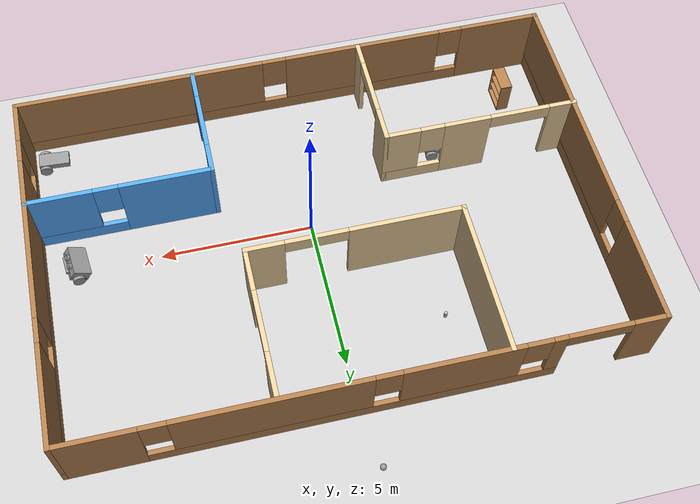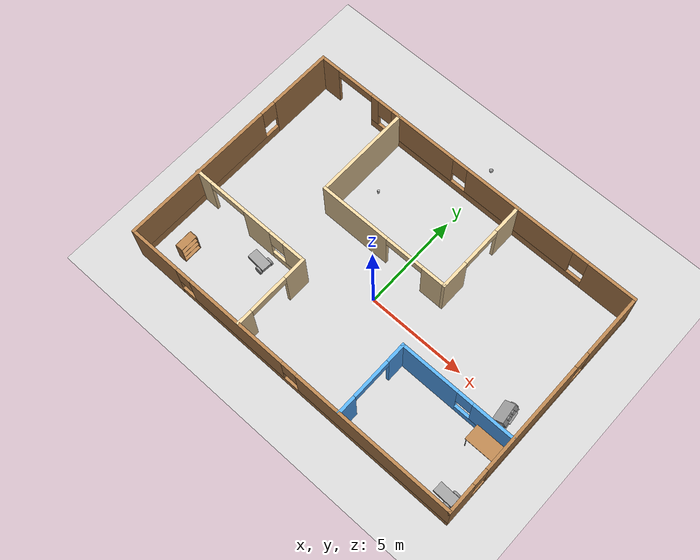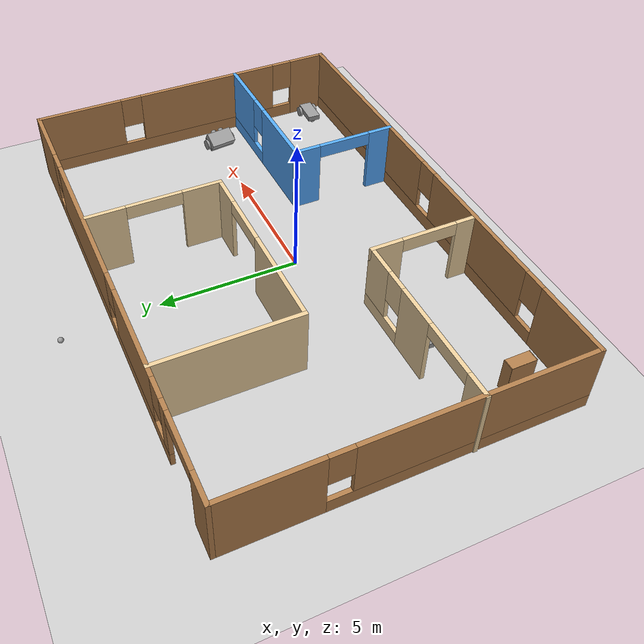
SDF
<sdf version="1.6">
 <world name="default">
  <plugin name="myplugin" filename="libhello.so"/>
  <light name="sun" type="directional">
   <pose>0 0 10 0 -0 0</pose>
   <diffuse>0.8 0.8 0.8 1</diffuse>
   <specular>0.2 0.2 0.2 1</specular>
   <attenuation>
    <range>1000</range>
    <constant>0.9</constant>
    <linear>0.01</linear>
    <quadratic>0.001</quadratic>
   </attenuation>
   <direction>-0.5 0.1 -0.9</direction>
  </light>
  <model name="ground_plane">
   <static>1</static>
   <link name="link">
    <collision name="collision">
     <geometry><plane><normal>0 0 1</normal><size>100 100</size></plane></geometry>
     <surface><friction><ode><mu>100</mu><mu2>50</mu2></ode></friction></surface>
    </collision>
    <visual name="visual">
     <cast_shadows>0</cast_shadows>
     <geometry><plane><normal>0 0 1</normal><size>100 100</size></plane></geometry>
     <material>
      <script><uri>file://media/materials/scripts/gazebo.material</uri><name>Gazebo/Grey</name></script>
     </material>
    </visual>
   </link>
  </model>
  <gravity>0 0 -9.8</gravity>
  <magnetic_field>6e-06 2.3e-05 -4.2e-05</magnetic_field>
  <atmosphere type="adiabatic"/>
  <physics name="default_physics" default="0" type="ode">
   <max_step_size>0.001</max_step_size>
   <real_time_factor>1</real_time_factor>
   <real_time_update_rate>1000</real_time_update_rate>
  </physics>
  <scene><ambient>0.4 0.4 0.4 1</ambient><background>0.7 0.7 0.7 1</background><shadows>1</shadows></scene>
  <spherical_coordinates>
   <surface_model>EARTH_WGS84</surface_model>
   <latitude_deg>0</latitude_deg>
   <longitude_deg>0</longitude_deg>
   <elevation>0</elevation>
   <heading_deg>0</heading_deg>
  </spherical_coordinates>
  <model name="beer">
   <link name="link">
    <pose>0 0 0.115 0 -0 0</pose>
    <inertial>
     <mass>0.39</mass>
     <inertia><ixx>0.00058</ixx><ixy>0</ixy><ixz>0</ixz><iyy>0.00058</iyy><iyz>0</iyz><izz>0.00019</izz></inertia>
    </inertial>
    <collision name="collision">
     <geometry><cylinder><radius>0.055</radius><length>0.23</length></cylinder></geometry>
    </collision>
    <visual name="visual">
     <geometry><cylinder><radius>0.055</radius><length>0.23</length></cylinder></geometry>
     <material>
      <script>
       <uri>model://beer/materials/scripts</uri>
       <uri>model://beer/materials/textures</uri>
       <name>Beer/Diffuse</name>
      </script>
     </material>
    </visual>
   </link>
   <pose>-3.40388 4.09892 -2e-06 0 0 -9e-06</pose>
  </model>
  <model name="table">
   <static>1</static>
   <link name="link">
    <collision name="surface">
     <pose>0 0 1 0 -0 0</pose>
     <geometry><box><size>1.5 0.8 0.03</size></box></geometry>
     <surface><friction><ode><mu>0.6</mu><mu2>0.6</mu2></ode></friction></surface>
    </collision>
    <visual name="visual1">
     <pose>0 0 1 0 -0 0</pose>
     <geometry><box><size>1.5 0.8 0.03</size></box></geometry>
     <material>
      <script><uri>file://media/materials/scripts/gazebo.material</uri><name>Gazebo/Wood</name></script>
     </material>
    </visual>
    <collision name="front_left_leg">
     <pose>0.68 0.38 0.5 0 -0 0</pose>
     <geometry><cylinder><radius>0.02</radius><length>1</length></cylinder></geometry>
    </collision>
    <visual name="front_left_leg">
     <pose>0.68 0.38 0.5 0 -0 0</pose>
     <geometry><cylinder><radius>0.02</radius><length>1</length></cylinder></geometry>
     <material>
      <script><uri>file://media/materials/scripts/gazebo.material</uri><name>Gazebo/Grey</name></script>
     </material>
    </visual>
    <collision name="front_right_leg">
     <pose>0.68 -0.38 0.5 0 -0 0</pose>
     <geometry><cylinder><radius>0.02</radius><length>1</length></cylinder></geometry>
    </collision>
    <visual name="front_right_leg">
     <pose>0.68 -0.38 0.5 0 -0 0</pose>
     <geometry><cylinder><radius>0.02</radius><length>1</length></cylinder></geometry>
     <material>
      <script><uri>file://media/materials/scripts/gazebo.material</uri><name>Gazebo/Grey</name></script>
     </material>
    </visual>
    <collision name="back_right_leg">
     <pose>-0.68 -0.38 0.5 0 -0 0</pose>
     <geometry><cylinder><radius>0.02</radius><length>1</length></cylinder></geometry>
    </collision>
    <visual name="back_right_leg">
     <pose>-0.68 -0.38 0.5 0 -0 0</pose>
     <geometry><cylinder><radius>0.02</radius><length>1</length></cylinder></geometry>
     <material>
      <script><uri>file://media/materials/scripts/gazebo.material</uri><name>Gazebo/Grey</name></script>
     </material>
    </visual>
    <collision name="back_left_leg">
     <pose>-0.68 0.38 0.5 0 -0 0</pose>
     <geometry><cylinder><radius>0.02</radius><length>1</length></cylinder></geometry>
    </collision>
    <visual name="back_left_leg">
     <pose>-0.68 0.38 0.5 0 -0 0</pose>
     <geometry><cylinder><radius>0.02</radius><length>1</length></cylinder></geometry>
     <material>
      <script><uri>file://media/materials/scripts/gazebo.material</uri><name>Gazebo/Grey</name></script>
     </material>
    </visual>
   </link>
   <pose>7.88767 -1.89128 0 0 -0 0</pose>
  </model>
  <model name="bookshelf">
   <link name="link">
    <pose>0 0 0 0 -0 1.5707</pose>
    <inertial>
     <mass>1</mass>
     <inertia><ixx>1</ixx><ixy>0</ixy><ixz>0</ixz><iyy>1</iyy><iyz>0</iyz><izz>1</izz></inertia>
    </inertial>
    <visual name="visual1">
     <pose>0 0.005 0.6 0 -0 0</pose>
     <geometry><box><size>0.9 0.01 1.2</size></box></geometry>
     <material>
      <script><uri>file://media/materials/scripts/gazebo.material</uri><name>Gazebo/Wood</name></script>
      <shader type="pixel"><normal_map>__default__</normal_map></shader>
      <ambient>1 1 1 1</ambient>
      <diffuse>1 1 1 1</diffuse>
      <specular>0.2 0.2 0.2 1</specular>
      <emissive>0 0 0 1</emissive>
     </material>
    </visual>
    <visual name="visual2">
     <pose>0.45 -0.195 0.6 0 -0 0</pose>
     <geometry><box><size>0.02 0.4 1.2</size></box></geometry>
     <material>
      <script><uri>file://media/materials/scripts/gazebo.material</uri><name>Gazebo/Wood</name></script>
      <shader type="pixel"><normal_map>__default__</normal_map></shader>
      <ambient>1 1 1 1</ambient>
      <diffuse>1 1 1 1</diffuse>
      <specular>0.2 0.2 0.2 1</specular>
      <emissive>0 0 0 1</emissive>
     </material>
    </visual>
    <visual name="visual3">
     <pose>-0.45 -0.195 0.6 0 -0 0</pose>
     <geometry><box><size>0.02 0.4 1.2</size></box></geometry>
     <material>
      <script><uri>file://media/materials/scripts/gazebo.material</uri><name>Gazebo/Wood</name></script>
      <shader type="pixel"><normal_map>__default__</normal_map></shader>
      <ambient>1 1 1 1</ambient>
      <diffuse>1 1 1 1</diffuse>
      <specular>0.2 0.2 0.2 1</specular>
      <emissive>0 0 0 1</emissive>
     </material>
    </visual>
    <visual name="visual4">
     <pose>0 -0.195 0.03 0 -0 0</pose>
     <geometry><box><size>0.88 0.4 0.06</size></box></geometry>
     <material>
      <script><uri>file://media/materials/scripts/gazebo.material</uri><name>Gazebo/Wood</name></script>
      <shader type="pixel"><normal_map>__default__</normal_map></shader>
      <ambient>1 1 1 1</ambient>
      <diffuse>1 1 1 1</diffuse>
      <specular>0.2 0.2 0.2 1</specular>
      <emissive>0 0 0 1</emissive>
     </material>
    </visual>
    <visual name="visual5">
     <pose>0 -0.195 1.19 0 -0 0</pose>
     <geometry><box><size>0.88 0.4 0.02</size></box></geometry>
     <material>
      <script><uri>file://media/materials/scripts/gazebo.material</uri><name>Gazebo/Wood</name></script>
      <shader type="pixel"><normal_map>__default__</normal_map></shader>
      <ambient>1 1 1 1</ambient>
      <diffuse>1 1 1 1</diffuse>
      <specular>0.2 0.2 0.2 1</specular>
      <emissive>0 0 0 1</emissive>
     </material>
    </visual>
    <visual name="visual6">
     <pose>0 -0.195 0.43 0 -0 0</pose>
     <geometry><box><size>0.88 0.4 0.02</size></box></geometry>
     <material>
      <script><uri>file://media/materials/scripts/gazebo.material</uri><name>Gazebo/Wood</name></script>
      <shader type="pixel"><normal_map>__default__</normal_map></shader>
      <ambient>1 1 1 1</ambient>
      <diffuse>1 1 1 1</diffuse>
      <specular>0.2 0.2 0.2 1</specular>
      <emissive>0 0 0 1</emissive>
     </material>
    </visual>
    <visual name="visual7">
     <pose>0 -0.195 0.8 0 -0 0</pose>
     <geometry><box><size>0.88 0.4 0.02</size></box></geometry>
     <material>
      <script><uri>file://media/materials/scripts/gazebo.material</uri><name>Gazebo/Wood</name></script>
      <shader type="pixel"><normal_map>__default__</normal_map></shader>
      <ambient>1 1 1 1</ambient>
      <diffuse>1 1 1 1</diffuse>
      <specular>0.2 0.2 0.2 1</specular>
      <emissive>0 0 0 1</emissive>
     </material>
    </visual>
    <collision name="back">
     <pose>0 0.005 0.6 0 -0 0</pose>
     <geometry><box><size>0.9 0.01 1.2</size></box></geometry>
     <surface>
      <friction>
       <ode><mu>1</mu><mu2>1</mu2><fdir1>0 0 0</fdir1><slip1>0</slip1><slip2>0</slip2></ode>
       <torsional>
        <coefficient>1</coefficient>
        <patch_radius>0</patch_radius>
        <surface_radius>0</surface_radius>
        <use_patch_radius>1</use_patch_radius>
        <ode><slip>0</slip></ode>
       </torsional>
      </friction>
      <bounce><restitution_coefficient>0</restitution_coefficient><threshold>1e+06</threshold></bounce>
      <contact>
       <collide_without_contact>0</collide_without_contact>
       <collide_without_contact_bitmask>1</collide_without_contact_bitmask>
       <collide_bitmask>1</collide_bitmask>
       <ode>
        <soft_cfm>0</soft_cfm>
        <soft_erp>0.2</soft_erp>
        <kp>1e+13</kp>
        <kd>1</kd>
        <max_vel>0.01</max_vel>
        <min_depth>0</min_depth>
       </ode>
       <bullet>
        <split_impulse>1</split_impulse>
        <split_impulse_penetration_threshold>-0.01</split_impulse_penetration_threshold>
        <soft_cfm>0</soft_cfm>
        <soft_erp>0.2</soft_erp>
        <kp>1e+13</kp>
        <kd>1</kd>
       </bullet>
      </contact>
     </surface>
    </collision>
    <collision name="left_side">
     <pose>0.45 -0.195 0.6 0 -0 0</pose>
     <geometry><box><size>0.02 0.4 1.2</size></box></geometry>
     <surface>
      <friction>
       <ode><mu>1</mu><mu2>1</mu2><fdir1>0 0 0</fdir1><slip1>0</slip1><slip2>0</slip2></ode>
       <torsional>
        <coefficient>1</coefficient>
        <patch_radius>0</patch_radius>
        <surface_radius>0</surface_radius>
        <use_patch_radius>1</use_patch_radius>
        <ode><slip>0</slip></ode>
       </torsional>
      </friction>
      <bounce><restitution_coefficient>0</restitution_coefficient><threshold>1e+06</threshold></bounce>
      <contact>
       <collide_without_contact>0</collide_without_contact>
       <collide_without_contact_bitmask>1</collide_without_contact_bitmask>
       <collide_bitmask>1</collide_bitmask>
       <ode>
        <soft_cfm>0</soft_cfm>
        <soft_erp>0.2</soft_erp>
        <kp>1e+13</kp>
        <kd>1</kd>
        <max_vel>0.01</max_vel>
        <min_depth>0</min_depth>
       </ode>
       <bullet>
        <split_impulse>1</split_impulse>
        <split_impulse_penetration_threshold>-0.01</split_impulse_penetration_threshold>
        <soft_cfm>0</soft_cfm>
        <soft_erp>0.2</soft_erp>
        <kp>1e+13</kp>
        <kd>1</kd>
       </bullet>
      </contact>
     </surface>
    </collision>
    <collision name="right_side">
     <pose>-0.45 -0.195 0.6 0 -0 0</pose>
     <geometry><box><size>0.02 0.4 1.2</size></box></geometry>
     <surface>
      <friction>
       <ode><mu>1</mu><mu2>1</mu2><fdir1>0 0 0</fdir1><slip1>0</slip1><slip2>0</slip2></ode>
       <torsional>
        <coefficient>1</coefficient>
        <patch_radius>0</patch_radius>
        <surface_radius>0</surface_radius>
        <use_patch_radius>1</use_patch_radius>
        <ode><slip>0</slip></ode>
       </torsional>
      </friction>
      <bounce><restitution_coefficient>0</restitution_coefficient><threshold>1e+06</threshold></bounce>
      <contact>
       <collide_without_contact>0</collide_without_contact>
       <collide_without_contact_bitmask>1</collide_without_contact_bitmask>
       <collide_bitmask>1</collide_bitmask>
       <ode>
        <soft_cfm>0</soft_cfm>
        <soft_erp>0.2</soft_erp>
        <kp>1e+13</kp>
        <kd>1</kd>
        <max_vel>0.01</max_vel>
        <min_depth>0</min_depth>
       </ode>
       <bullet>
        <split_impulse>1</split_impulse>
        <split_impulse_penetration_threshold>-0.01</split_impulse_penetration_threshold>
        <soft_cfm>0</soft_cfm>
        <soft_erp>0.2</soft_erp>
        <kp>1e+13</kp>
        <kd>1</kd>
       </bullet>
      </contact>
     </surface>
    </collision>
    <collision name="high_shelf">
     <pose>0 -0.195 0.8 0 -0 0</pose>
     <geometry><box><size>0.88 0.4 0.02</size></box></geometry>
     <surface>
      <friction>
       <ode><mu>1</mu><mu2>1</mu2><fdir1>0 0 0</fdir1><slip1>0</slip1><slip2>0</slip2></ode>
       <torsional>
        <coefficient>1</coefficient>
        <patch_radius>0</patch_radius>
        <surface_radius>0</surface_radius>
        <use_patch_radius>1</use_patch_radius>
        <ode><slip>0</slip></ode>
       </torsional>
      </friction>
      <bounce><restitution_coefficient>0</restitution_coefficient><threshold>1e+06</threshold></bounce>
      <contact>
       <collide_without_contact>0</collide_without_contact>
       <collide_without_contact_bitmask>1</collide_without_contact_bitmask>
       <collide_bitmask>1</collide_bitmask>
       <ode>
        <soft_cfm>0</soft_cfm>
        <soft_erp>0.2</soft_erp>
        <kp>1e+13</kp>
        <kd>1</kd>
        <max_vel>0.01</max_vel>
        <min_depth>0</min_depth>
       </ode>
       <bullet>
        <split_impulse>1</split_impulse>
        <split_impulse_penetration_threshold>-0.01</split_impulse_penetration_threshold>
        <soft_cfm>0</soft_cfm>
        <soft_erp>0.2</soft_erp>
        <kp>1e+13</kp>
        <kd>1</kd>
       </bullet>
      </contact>
     </surface>
    </collision>
    <collision name="bottom">
     <pose>0 -0.195 0.03 0 -0 0</pose>
     <geometry><box><size>0.88 0.4 0.06</size></box></geometry>
     <surface>
      <friction>
       <ode><mu>1</mu><mu2>1</mu2><fdir1>0 0 0</fdir1><slip1>0</slip1><slip2>0</slip2></ode>
       <torsional>
        <coefficient>1</coefficient>
        <patch_radius>0</patch_radius>
        <surface_radius>0</surface_radius>
        <use_patch_radius>1</use_patch_radius>
        <ode><slip>0</slip></ode>
       </torsional>
      </friction>
      <bounce><restitution_coefficient>0</restitution_coefficient><threshold>1e+06</threshold></bounce>
      <contact>
       <collide_without_contact>0</collide_without_contact>
       <collide_without_contact_bitmask>1</collide_without_contact_bitmask>
       <collide_bitmask>1</collide_bitmask>
       <ode>
        <soft_cfm>0</soft_cfm>
        <soft_erp>0.2</soft_erp>
        <kp>1e+13</kp>
        <kd>1</kd>
        <max_vel>0.01</max_vel>
        <min_depth>0</min_depth>
       </ode>
       <bullet>
        <split_impulse>1</split_impulse>
        <split_impulse_penetration_threshold>-0.01</split_impulse_penetration_threshold>
        <soft_cfm>0</soft_cfm>
        <soft_erp>0.2</soft_erp>
        <kp>1e+13</kp>
        <kd>1</kd>
       </bullet>
      </contact>
     </surface>
    </collision>
    <collision name="top">
     <pose>0 -0.195 1.19 0 -0 0</pose>
     <geometry><box><size>0.88 0.4 0.02</size></box></geometry>
     <surface>
      <friction>
       <ode><mu>1</mu><mu2>1</mu2><fdir1>0 0 0</fdir1><slip1>0</slip1><slip2>0</slip2></ode>
       <torsional>
        <coefficient>1</coefficient>
        <patch_radius>0</patch_radius>
        <surface_radius>0</surface_radius>
        <use_patch_radius>1</use_patch_radius>
        <ode><slip>0</slip></ode>
       </torsional>
      </friction>
      <bounce><restitution_coefficient>0</restitution_coefficient><threshold>1e+06</threshold></bounce>
      <contact>
       <collide_without_contact>0</collide_without_contact>
       <collide_without_contact_bitmask>1</collide_without_contact_bitmask>
       <collide_bitmask>1</collide_bitmask>
       <ode>
        <soft_cfm>0</soft_cfm>
        <soft_erp>0.2</soft_erp>
        <kp>1e+13</kp>
        <kd>1</kd>
        <max_vel>0.01</max_vel>
        <min_depth>0</min_depth>
       </ode>
       <bullet>
        <split_impulse>1</split_impulse>
        <split_impulse_penetration_threshold>-0.01</split_impulse_penetration_threshold>
        <soft_cfm>0</soft_cfm>
        <soft_erp>0.2</soft_erp>
        <kp>1e+13</kp>
        <kd>1</kd>
       </bullet>
      </contact>
     </surface>
    </collision>
    <collision name="low_shelf">
     <pose>0 -0.195 0.43 0 -0 0</pose>
     <geometry><box><size>0.88 0.4 0.02</size></box></geometry>
     <surface>
      <friction>
       <ode><mu>1</mu><mu2>1</mu2><fdir1>0 0 0</fdir1><slip1>0</slip1><slip2>0</slip2></ode>
       <torsional>
        <coefficient>1</coefficient>
        <patch_radius>0</patch_radius>
        <surface_radius>0</surface_radius>
        <use_patch_radius>1</use_patch_radius>
        <ode><slip>0</slip></ode>
       </torsional>
      </friction>
      <bounce><restitution_coefficient>0</restitution_coefficient><threshold>1e+06</threshold></bounce>
      <contact>
       <collide_without_contact>0</collide_without_contact>
       <collide_without_contact_bitmask>1</collide_without_contact_bitmask>
       <collide_bitmask>1</collide_bitmask>
       <ode>
        <soft_cfm>0</soft_cfm>
        <soft_erp>0.2</soft_erp>
        <kp>1e+13</kp>
        <kd>1</kd>
        <max_vel>0.01</max_vel>
        <min_depth>0</min_depth>
       </ode>
       <bullet>
        <split_impulse>1</split_impulse>
        <split_impulse_penetration_threshold>-0.01</split_impulse_penetration_threshold>
        <soft_cfm>0</soft_cfm>
        <soft_erp>0.2</soft_erp>
        <kp>1e+13</kp>
        <kd>1</kd>
       </bullet>
      </contact>
     </surface>
    </collision>
   </link>
   <static>1</static>
   <pose>-7.86837 -3.77974 0 0 -0 0</pose>
  </model>
  <model name="robot_2">
   <link name="link_0">
    <inertial>
     <mass>1</mass>
     <inertia>
      <ixx>0.166667</ixx>
      <ixy>0</ixy>
      <ixz>0</ixz>
      <iyy>0.166667</iyy>
      <iyz>0</iyz>
      <izz>0.166667</izz>
     </inertia>
    </inertial>
    <visual name="visual">
     <geometry><box><size>0.6 1 0.1</size></box></geometry>
     <material>
      <lighting>1</lighting>
      <script><uri>file://media/materials/scripts/gazebo.material</uri><name>Gazebo/Grey</name></script>
      <shader type="pixel"><normal_map>__default__</normal_map></shader>
      <ambient>0.3 0.3 0.3 1</ambient>
      <diffuse>0.7 0.7 0.7 1</diffuse>
      <specular>0.01 0.01 0.01 1</specular>
      <emissive>0 0 0 1</emissive>
     </material>
    </visual>
    <collision name="collision">
     <geometry><box><size>0.6 1 0.1</size></box></geometry>
     <surface>
      <friction>
       <ode><mu>1</mu><mu2>1</mu2><fdir1>0 0 0</fdir1><slip1>0</slip1><slip2>0</slip2></ode>
       <torsional>
        <coefficient>1</coefficient>
        <patch_radius>0</patch_radius>
        <surface_radius>0</surface_radius>
        <use_patch_radius>1</use_patch_radius>
        <ode><slip>0</slip></ode>
       </torsional>
      </friction>
      <bounce><restitution_coefficient>0</restitution_coefficient><threshold>1e+06</threshold></bounce>
      <contact>
       <collide_without_contact>0</collide_without_contact>
       <collide_without_contact_bitmask>1</collide_without_contact_bitmask>
       <collide_bitmask>1</collide_bitmask>
       <ode>
        <soft_cfm>0</soft_cfm>
        <soft_erp>0.2</soft_erp>
        <kp>1e+13</kp>
        <kd>1</kd>
        <max_vel>0.01</max_vel>
        <min_depth>0</min_depth>
       </ode>
       <bullet>
        <split_impulse>1</split_impulse>
        <split_impulse_penetration_threshold>-0.01</split_impulse_penetration_threshold>
        <soft_cfm>0</soft_cfm>
        <soft_erp>0.2</soft_erp>
        <kp>1e+13</kp>
        <kd>1</kd>
       </bullet>
      </contact>
     </surface>
    </collision>
   </link>
   <link name="link_1">
    <pose>-0 -0.550019 -0 1.5707 -0 0</pose>
    <inertial>
     <mass>1</mass>
     <inertia><ixx>0.145833</ixx><ixy>0</ixy><ixz>0</ixz><iyy>0.145833</iyy><iyz>0</iyz><izz>0.125</izz></inertia>
    </inertial>
    <visual name="visual">
     <geometry><cylinder><radius>0.2</radius><length>0.1</length></cylinder></geometry>
     <material>
      <lighting>1</lighting>
      <script><uri>file://media/materials/scripts/gazebo.material</uri><name>Gazebo/Grey</name></script>
      <shader type="pixel"><normal_map>__default__</normal_map></shader>
      <ambient>0.3 0.3 0.3 1</ambient>
      <diffuse>0.7 0.7 0.7 1</diffuse>
      <specular>0.01 0.01 0.01 1</specular>
      <emissive>0 0 0 1</emissive>
     </material>
    </visual>
    <collision name="collision">
     <geometry><cylinder><radius>0.2</radius><length>0.1</length></cylinder></geometry>
     <surface>
      <friction>
       <ode><mu>1</mu><mu2>1</mu2><fdir1>0 0 0</fdir1><slip1>0</slip1><slip2>0</slip2></ode>
       <torsional>
        <coefficient>1</coefficient>
        <patch_radius>0</patch_radius>
        <surface_radius>0</surface_radius>
        <use_patch_radius>1</use_patch_radius>
        <ode><slip>0</slip></ode>
       </torsional>
      </friction>
      <bounce><restitution_coefficient>0</restitution_coefficient><threshold>1e+06</threshold></bounce>
      <contact>
       <collide_without_contact>0</collide_without_contact>
       <collide_without_contact_bitmask>1</collide_without_contact_bitmask>
       <collide_bitmask>1</collide_bitmask>
       <ode>
        <soft_cfm>0</soft_cfm>
        <soft_erp>0.2</soft_erp>
        <kp>1e+13</kp>
        <kd>1</kd>
        <max_vel>0.01</max_vel>
        <min_depth>0</min_depth>
       </ode>
       <bullet>
        <split_impulse>1</split_impulse>
        <split_impulse_penetration_threshold>-0.01</split_impulse_penetration_threshold>
        <soft_cfm>0</soft_cfm>
        <soft_erp>0.2</soft_erp>
        <kp>1e+13</kp>
        <kd>1</kd>
       </bullet>
      </contact>
     </surface>
    </collision>
   </link>
   <link name="link_1_0">
    <pose>-2.6e-05 -0 0.200078 0 0.000173 -9.4e-05</pose>
    <inertial>
     <mass>1</mass>
     <inertia>
      <ixx>0.166667</ixx>
      <ixy>0</ixy>
      <ixz>0</ixz>
      <iyy>0.166667</iyy>
      <iyz>0</iyz>
      <izz>0.166667</izz>
     </inertia>
    </inertial>
    <visual name="visual">
     <geometry><box><size>0.6 1 0.3</size></box></geometry>
     <material>
      <lighting>1</lighting>
      <script><uri>file://media/materials/scripts/gazebo.material</uri><name>Gazebo/Grey</name></script>
      <shader type="pixel"><normal_map>__default__</normal_map></shader>
      <ambient>0.3 0.3 0.3 1</ambient>
      <diffuse>0.7 0.7 0.7 1</diffuse>
      <specular>0.01 0.01 0.01 1</specular>
      <emissive>0 0 0 1</emissive>
     </material>
    </visual>
    <collision name="collision">
     <geometry><box><size>0.6 1 0.3</size></box></geometry>
     <surface>
      <friction>
       <ode><mu>1</mu><mu2>1</mu2><fdir1>0 0 0</fdir1><slip1>0</slip1><slip2>0</slip2></ode>
       <torsional>
        <coefficient>1</coefficient>
        <patch_radius>0</patch_radius>
        <surface_radius>0</surface_radius>
        <use_patch_radius>1</use_patch_radius>
        <ode><slip>0</slip></ode>
       </torsional>
      </friction>
      <bounce><restitution_coefficient>0</restitution_coefficient><threshold>1e+06</threshold></bounce>
      <contact>
       <collide_without_contact>0</collide_without_contact>
       <collide_without_contact_bitmask>1</collide_without_contact_bitmask>
       <collide_bitmask>1</collide_bitmask>
       <ode>
        <soft_cfm>0</soft_cfm>
        <soft_erp>0.2</soft_erp>
        <kp>1e+13</kp>
        <kd>1</kd>
        <max_vel>0.01</max_vel>
        <min_depth>0</min_depth>
       </ode>
       <bullet>
        <split_impulse>1</split_impulse>
        <split_impulse_penetration_threshold>-0.01</split_impulse_penetration_threshold>
        <soft_cfm>0</soft_cfm>
        <soft_erp>0.2</soft_erp>
        <kp>1e+13</kp>
        <kd>1</kd>
       </bullet>
      </contact>
     </surface>
    </collision>
   </link>
   <link name="link_1_clone">
    <pose>0 0.550019 -0 1.5707 -0 0</pose>
    <inertial>
     <mass>1</mass>
     <inertia><ixx>0.145833</ixx><ixy>0</ixy><ixz>0</ixz><iyy>0.145833</iyy><iyz>0</iyz><izz>0.125</izz></inertia>
    </inertial>
    <visual name="visual">
     <geometry><cylinder><radius>0.2</radius><length>0.1</length></cylinder></geometry>
     <material>
      <lighting>1</lighting>
      <script><uri>file://media/materials/scripts/gazebo.material</uri><name>Gazebo/Grey</name></script>
      <shader type="pixel"><normal_map>__default__</normal_map></shader>
      <ambient>0.3 0.3 0.3 1</ambient>
      <diffuse>0.7 0.7 0.7 1</diffuse>
      <specular>0.01 0.01 0.01 1</specular>
      <emissive>0 0 0 1</emissive>
     </material>
    </visual>
    <collision name="collision">
     <geometry><cylinder><radius>0.2</radius><length>0.1</length></cylinder></geometry>
     <surface>
      <friction>
       <ode><mu>1</mu><mu2>1</mu2><fdir1>0 0 0</fdir1><slip1>0</slip1><slip2>0</slip2></ode>
       <torsional>
        <coefficient>1</coefficient>
        <patch_radius>0</patch_radius>
        <surface_radius>0</surface_radius>
        <use_patch_radius>1</use_patch_radius>
        <ode><slip>0</slip></ode>
       </torsional>
      </friction>
      <bounce><restitution_coefficient>0</restitution_coefficient><threshold>1e+06</threshold></bounce>
      <contact>
       <collide_without_contact>0</collide_without_contact>
       <collide_without_contact_bitmask>1</collide_without_contact_bitmask>
       <collide_bitmask>1</collide_bitmask>
       <ode>
        <soft_cfm>0</soft_cfm>
        <soft_erp>0.2</soft_erp>
        <kp>1e+13</kp>
        <kd>1</kd>
        <max_vel>0.01</max_vel>
        <min_depth>0</min_depth>
       </ode>
       <bullet>
        <split_impulse>1</split_impulse>
        <split_impulse_penetration_threshold>-0.01</split_impulse_penetration_threshold>
        <soft_cfm>0</soft_cfm>
        <soft_erp>0.2</soft_erp>
        <kp>1e+13</kp>
        <kd>1</kd>
       </bullet>
      </contact>
     </surface>
    </collision>
   </link>
   <link name="link_6_clone">
    <pose>0.342887 0.163126 0.243557 1.5707 3e-06 1.5707</pose>
    <inertial>
     <mass>1e-05</mass>
     <inertia><ixx>0.145833</ixx><ixy>0</ixy><ixz>0</ixz><iyy>0.145833</iyy><iyz>0</iyz><izz>0.125</izz></inertia>
    </inertial>
    <visual name="visual">
     <geometry><cylinder><radius>0.1</radius><length>0.1</length></cylinder></geometry>
     <material>
      <lighting>1</lighting>
      <script><uri>file://media/materials/scripts/gazebo.material</uri><name>Gazebo/Grey</name></script>
      <shader type="pixel"><normal_map>__default__</normal_map></shader>
      <ambient>0.3 0.3 0.3 1</ambient>
      <diffuse>0.7 0.7 0.7 1</diffuse>
      <specular>0.01 0.01 0.01 1</specular>
      <emissive>0 0 0 1</emissive>
     </material>
    </visual>
    <collision name="collision">
     <geometry><cylinder><radius>0.1</radius><length>0.1</length></cylinder></geometry>
     <surface>
      <friction>
       <ode><mu>1</mu><mu2>1</mu2><fdir1>0 0 0</fdir1><slip1>0</slip1><slip2>0</slip2></ode>
       <torsional>
        <coefficient>1</coefficient>
        <patch_radius>0</patch_radius>
        <surface_radius>0</surface_radius>
        <use_patch_radius>1</use_patch_radius>
        <ode><slip>0</slip></ode>
       </torsional>
      </friction>
      <bounce><restitution_coefficient>0</restitution_coefficient><threshold>1e+06</threshold></bounce>
      <contact>
       <collide_without_contact>0</collide_without_contact>
       <collide_without_contact_bitmask>1</collide_without_contact_bitmask>
       <collide_bitmask>1</collide_bitmask>
       <ode>
        <soft_cfm>0</soft_cfm>
        <soft_erp>0.2</soft_erp>
        <kp>1e+13</kp>
        <kd>1</kd>
        <max_vel>0.01</max_vel>
        <min_depth>0</min_depth>
       </ode>
       <bullet>
        <split_impulse>1</split_impulse>
        <split_impulse_penetration_threshold>-0.01</split_impulse_penetration_threshold>
        <soft_cfm>0</soft_cfm>
        <soft_erp>0.2</soft_erp>
        <kp>1e+13</kp>
        <kd>1</kd>
       </bullet>
      </contact>
     </surface>
    </collision>
   </link>
   <link name="link_6_clone_clone">
    <pose>0.339801 -0.152965 0.239143 1.5707 1e-06 1.5707</pose>
    <inertial>
     <mass>1e-05</mass>
     <inertia><ixx>0.145833</ixx><ixy>0</ixy><ixz>0</ixz><iyy>0.145833</iyy><iyz>0</iyz><izz>0.125</izz></inertia>
    </inertial>
    <visual name="visual">
     <geometry><cylinder><radius>0.1</radius><length>0.1</length></cylinder></geometry>
     <material>
      <lighting>1</lighting>
      <script><uri>file://media/materials/scripts/gazebo.material</uri><name>Gazebo/Grey</name></script>
      <shader type="pixel"><normal_map>__default__</normal_map></shader>
      <ambient>0.3 0.3 0.3 1</ambient>
      <diffuse>0.7 0.7 0.7 1</diffuse>
      <specular>0.01 0.01 0.01 1</specular>
      <emissive>0 0 0 1</emissive>
     </material>
    </visual>
    <collision name="collision">
     <geometry><cylinder><radius>0.1</radius><length>0.1</length></cylinder></geometry>
     <surface>
      <friction>
       <ode><mu>1</mu><mu2>1</mu2><fdir1>0 0 0</fdir1><slip1>0</slip1><slip2>0</slip2></ode>
       <torsional>
        <coefficient>1</coefficient>
        <patch_radius>0</patch_radius>
        <surface_radius>0</surface_radius>
        <use_patch_radius>1</use_patch_radius>
        <ode><slip>0</slip></ode>
       </torsional>
      </friction>
      <bounce><restitution_coefficient>0</restitution_coefficient><threshold>1e+06</threshold></bounce>
      <contact>
       <collide_without_contact>0</collide_without_contact>
       <collide_without_contact_bitmask>1</collide_without_contact_bitmask>
       <collide_bitmask>1</collide_bitmask>
       <ode>
        <soft_cfm>0</soft_cfm>
        <soft_erp>0.2</soft_erp>
        <kp>1e+13</kp>
        <kd>1</kd>
        <max_vel>0.01</max_vel>
        <min_depth>0</min_depth>
       </ode>
       <bullet>
        <split_impulse>1</split_impulse>
        <split_impulse_penetration_threshold>-0.01</split_impulse_penetration_threshold>
        <soft_cfm>0</soft_cfm>
        <soft_erp>0.2</soft_erp>
        <kp>1e+13</kp>
        <kd>1</kd>
       </bullet>
      </contact>
     </surface>
    </collision>
   </link>
   <link name="link_7">
    <pose>0.351071 -5.4e-05 0.039446 1.5707 -0 0</pose>
    <inertial>
     <mass>1e-06</mass>
     <inertia><ixx>0.145833</ixx><ixy>0</ixy><ixz>0</ixz><iyy>0.145833</iyy><iyz>0</iyz><izz>0.125</izz></inertia>
    </inertial>
    <visual name="visual">
     <geometry><cylinder><radius>0.05</radius><length>0.6</length></cylinder></geometry>
     <material>
      <lighting>1</lighting>
      <script><uri>file://media/materials/scripts/gazebo.material</uri><name>Gazebo/Grey</name></script>
      <shader type="pixel"><normal_map>__default__</normal_map></shader>
      <ambient>0.3 0.3 0.3 1</ambient>
      <diffuse>0.7 0.7 0.7 1</diffuse>
      <specular>0.01 0.01 0.01 1</specular>
      <emissive>0 0 0 1</emissive>
     </material>
    </visual>
    <collision name="collision">
     <geometry><cylinder><radius>0.05</radius><length>0.6</length></cylinder></geometry>
     <surface>
      <friction>
       <ode><mu>1</mu><mu2>1</mu2><fdir1>0 0 0</fdir1><slip1>0</slip1><slip2>0</slip2></ode>
       <torsional>
        <coefficient>1</coefficient>
        <patch_radius>0</patch_radius>
        <surface_radius>0</surface_radius>
        <use_patch_radius>1</use_patch_radius>
        <ode><slip>0</slip></ode>
       </torsional>
      </friction>
      <bounce><restitution_coefficient>0</restitution_coefficient><threshold>1e+06</threshold></bounce>
      <contact>
       <collide_without_contact>0</collide_without_contact>
       <collide_without_contact_bitmask>1</collide_without_contact_bitmask>
       <collide_bitmask>1</collide_bitmask>
       <ode>
        <soft_cfm>0</soft_cfm>
        <soft_erp>0.2</soft_erp>
        <kp>1e+13</kp>
        <kd>1</kd>
        <max_vel>0.01</max_vel>
        <min_depth>0</min_depth>
       </ode>
       <bullet>
        <split_impulse>1</split_impulse>
        <split_impulse_penetration_threshold>-0.01</split_impulse_penetration_threshold>
        <soft_cfm>0</soft_cfm>
        <soft_erp>0.2</soft_erp>
        <kp>1e+13</kp>
        <kd>1</kd>
       </bullet>
      </contact>
     </surface>
    </collision>
   </link>
   <joint name="link_0_JOINT_0" type="revolute">
    <parent>link_0</parent>
    <child>link_1_clone</child>
    <axis>
     <xyz>0 0 1</xyz>
     <use_parent_model_frame>0</use_parent_model_frame>
     <limit>
      <lower>-1.79769e+308</lower>
      <upper>1.79769e+308</upper>
      <effort>-1</effort>
      <velocity>-1</velocity>
     </limit>
     <dynamics>
      <spring_reference>0</spring_reference>
      <spring_stiffness>0</spring_stiffness>
      <damping>0</damping>
      <friction>0</friction>
     </dynamics>
    </axis>
    <physics>
     <ode><limit><cfm>0</cfm><erp>0.2</erp></limit><suspension><cfm>0</cfm><erp>0.2</erp></suspension></ode>
    </physics>
   </joint>
   <joint name="link_0_JOINT_1" type="revolute">
    <parent>link_0</parent>
    <child>link_1</child>
    <axis>
     <xyz>0 0 1</xyz>
     <use_parent_model_frame>0</use_parent_model_frame>
     <limit>
      <lower>-1.79769e+308</lower>
      <upper>1.79769e+308</upper>
      <effort>-1</effort>
      <velocity>-1</velocity>
     </limit>
     <dynamics>
      <spring_reference>0</spring_reference>
      <spring_stiffness>0</spring_stiffness>
      <damping>0</damping>
      <friction>0</friction>
     </dynamics>
    </axis>
    <physics>
     <ode><limit><cfm>0</cfm><erp>0.2</erp></limit><suspension><cfm>0</cfm><erp>0.2</erp></suspension></ode>
    </physics>
   </joint>
   <joint name="link_0_JOINT_3" type="fixed">
    <parent>link_0</parent>
    <child>link_1_0</child>
    <physics>
     <ode><limit><cfm>0</cfm><erp>0.2</erp></limit><suspension><cfm>0</cfm><erp>0.2</erp></suspension></ode>
    </physics>
   </joint>
   <joint name="link_1_0_JOINT_7" type="fixed">
    <parent>link_1_0</parent>
    <child>link_6_clone_clone</child>
    <physics>
     <ode><limit><cfm>0</cfm><erp>0.2</erp></limit><suspension><cfm>0</cfm><erp>0.2</erp></suspension></ode>
    </physics>
   </joint>
   <joint name="link_1_0_JOINT_8" type="fixed">
    <parent>link_1_0</parent>
    <child>link_6_clone</child>
    <physics>
     <ode><limit><cfm>0</cfm><erp>0.2</erp></limit><suspension><cfm>0</cfm><erp>0.2</erp></suspension></ode>
    </physics>
   </joint>
   <joint name="link_1_0_JOINT_9" type="fixed">
    <parent>link_1_0</parent>
    <child>link_7</child>
    <physics>
     <ode><limit><cfm>0</cfm><erp>0.2</erp></limit><suspension><cfm>0</cfm><erp>0.2</erp></suspension></ode>
    </physics>
   </joint>
   <static>0</static>
   <pose>7.73553 -0.166689 0.199998 0 -0.552491 0.115979</pose>
  </model>
  <model name="robot_1">
   <link name="link_0">
    <pose>0 0.015 0.1 0 -0 0</pose>
    <inertial>
     <mass>1</mass>
     <inertia>
      <ixx>0.166667</ixx>
      <ixy>0</ixy>
      <ixz>0</ixz>
      <iyy>0.166667</iyy>
      <iyz>0</iyz>
      <izz>0.166667</izz>
     </inertia>
    </inertial>
    <visual name="visual">
     <geometry><box><size>1 0.5 0.2</size></box></geometry>
     <material>
      <lighting>1</lighting>
      <script><uri>file://media/materials/scripts/gazebo.material</uri><name>Gazebo/Grey</name></script>
      <shader type="pixel"><normal_map>__default__</normal_map></shader>
      <ambient>0.3 0.3 0.3 1</ambient>
      <diffuse>0.7 0.7 0.7 1</diffuse>
      <specular>0.01 0.01 0.01 1</specular>
      <emissive>0 0 0 1</emissive>
     </material>
    </visual>
    <collision name="collision">
     <geometry><box><size>1 0.5 0.2</size></box></geometry>
     <surface>
      <friction>
       <ode><mu>1</mu><mu2>1</mu2><fdir1>0 0 0</fdir1><slip1>0</slip1><slip2>0</slip2></ode>
       <torsional>
        <coefficient>1</coefficient>
        <patch_radius>0</patch_radius>
        <surface_radius>0</surface_radius>
        <use_patch_radius>1</use_patch_radius>
        <ode><slip>0</slip></ode>
       </torsional>
      </friction>
      <bounce><restitution_coefficient>0</restitution_coefficient><threshold>1e+06</threshold></bounce>
      <contact>
       <collide_without_contact>0</collide_without_contact>
       <collide_without_contact_bitmask>1</collide_without_contact_bitmask>
       <collide_bitmask>1</collide_bitmask>
       <ode>
        <soft_cfm>0</soft_cfm>
        <soft_erp>0.2</soft_erp>
        <kp>1e+13</kp>
        <kd>1</kd>
        <max_vel>0.01</max_vel>
        <min_depth>0</min_depth>
       </ode>
       <bullet>
        <split_impulse>1</split_impulse>
        <split_impulse_penetration_threshold>-0.01</split_impulse_penetration_threshold>
        <soft_cfm>0</soft_cfm>
        <soft_erp>0.2</soft_erp>
        <kp>1e+13</kp>
        <kd>1</kd>
       </bullet>
      </contact>
     </surface>
    </collision>
   </link>
   <link name="link_0_0">
    <pose>-0.303762 0.015004 -0.03228 -6e-06 0.013869 -1.7e-05</pose>
    <inertial>
     <mass>1</mass>
     <inertia><ixx>0.1</ixx><ixy>0</ixy><ixz>0</ixz><iyy>0.1</iyy><iyz>0</iyz><izz>0.1</izz></inertia>
    </inertial>
    <visual name="visual">
     <geometry><sphere><radius>0.15</radius></sphere></geometry>
     <material>
      <lighting>1</lighting>
      <script><uri>file://media/materials/scripts/gazebo.material</uri><name>Gazebo/Grey</name></script>
      <shader type="pixel"><normal_map>__default__</normal_map></shader>
      <ambient>0.3 0.3 0.3 1</ambient>
      <diffuse>0.7 0.7 0.7 1</diffuse>
      <specular>0.01 0.01 0.01 1</specular>
      <emissive>0 0 0 1</emissive>
     </material>
    </visual>
    <collision name="collision">
     <geometry><sphere><radius>0.15</radius></sphere></geometry>
     <surface>
      <friction>
       <ode><mu>1</mu><mu2>1</mu2><fdir1>0 0 0</fdir1><slip1>0</slip1><slip2>0</slip2></ode>
       <torsional>
        <coefficient>1</coefficient>
        <patch_radius>0</patch_radius>
        <surface_radius>0</surface_radius>
        <use_patch_radius>1</use_patch_radius>
        <ode><slip>0</slip></ode>
       </torsional>
      </friction>
      <bounce><restitution_coefficient>0</restitution_coefficient><threshold>1e+06</threshold></bounce>
      <contact>
       <collide_without_contact>0</collide_without_contact>
       <collide_without_contact_bitmask>1</collide_without_contact_bitmask>
       <collide_bitmask>1</collide_bitmask>
       <ode>
        <soft_cfm>0</soft_cfm>
        <soft_erp>0.2</soft_erp>
        <kp>1e+13</kp>
        <kd>1</kd>
        <max_vel>0.01</max_vel>
        <min_depth>0</min_depth>
       </ode>
       <bullet>
        <split_impulse>1</split_impulse>
        <split_impulse_penetration_threshold>-0.01</split_impulse_penetration_threshold>
        <soft_cfm>0</soft_cfm>
        <soft_erp>0.2</soft_erp>
        <kp>1e+13</kp>
        <kd>1</kd>
       </bullet>
      </contact>
     </surface>
    </collision>
   </link>
   <link name="link_1">
    <pose>0.297167 -0.300036 -0.004123 1.5707 -0 0</pose>
    <inertial>
     <mass>1</mass>
     <inertia><ixx>0.145833</ixx><ixy>0</ixy><ixz>0</ixz><iyy>0.145833</iyy><iyz>0</iyz><izz>0.125</izz></inertia>
    </inertial>
    <visual name="visual">
     <geometry><cylinder><radius>0.2</radius><length>0.1</length></cylinder></geometry>
     <material>
      <lighting>1</lighting>
      <script><uri>file://media/materials/scripts/gazebo.material</uri><name>Gazebo/Grey</name></script>
      <shader type="pixel"><normal_map>__default__</normal_map></shader>
      <ambient>0.3 0.3 0.3 1</ambient>
      <diffuse>0.7 0.7 0.7 1</diffuse>
      <specular>0.01 0.01 0.01 1</specular>
      <emissive>0 0 0 1</emissive>
     </material>
    </visual>
    <collision name="collision">
     <geometry><cylinder><radius>0.2</radius><length>0.1</length></cylinder></geometry>
     <surface>
      <friction>
       <ode><mu>1</mu><mu2>1</mu2><fdir1>0 0 0</fdir1><slip1>0</slip1><slip2>0</slip2></ode>
       <torsional>
        <coefficient>1</coefficient>
        <patch_radius>0</patch_radius>
        <surface_radius>0</surface_radius>
        <use_patch_radius>1</use_patch_radius>
        <ode><slip>0</slip></ode>
       </torsional>
      </friction>
      <bounce><restitution_coefficient>0</restitution_coefficient><threshold>1e+06</threshold></bounce>
      <contact>
       <collide_without_contact>0</collide_without_contact>
       <collide_without_contact_bitmask>1</collide_without_contact_bitmask>
       <collide_bitmask>1</collide_bitmask>
       <ode>
        <soft_cfm>0</soft_cfm>
        <soft_erp>0.2</soft_erp>
        <kp>1e+13</kp>
        <kd>1</kd>
        <max_vel>0.01</max_vel>
        <min_depth>0</min_depth>
       </ode>
       <bullet>
        <split_impulse>1</split_impulse>
        <split_impulse_penetration_threshold>-0.01</split_impulse_penetration_threshold>
        <soft_cfm>0</soft_cfm>
        <soft_erp>0.2</soft_erp>
        <kp>1e+13</kp>
        <kd>1</kd>
       </bullet>
      </contact>
     </surface>
    </collision>
   </link>
   <link name="link_1_clone">
    <pose>0.297178 0.330449 -0.004121 1.5707 -0 0</pose>
    <inertial>
     <mass>1</mass>
     <inertia><ixx>0.145833</ixx><ixy>0</ixy><ixz>0</ixz><iyy>0.145833</iyy><iyz>0</iyz><izz>0.125</izz></inertia>
    </inertial>
    <visual name="visual">
     <geometry><cylinder><radius>0.2</radius><length>0.1</length></cylinder></geometry>
     <material>
      <lighting>1</lighting>
      <script><uri>file://media/materials/scripts/gazebo.material</uri><name>Gazebo/Grey</name></script>
      <shader type="pixel"><normal_map>__default__</normal_map></shader>
      <ambient>0.3 0.3 0.3 1</ambient>
      <diffuse>0.7 0.7 0.7 1</diffuse>
      <specular>0.01 0.01 0.01 1</specular>
      <emissive>0 0 0 1</emissive>
     </material>
    </visual>
    <collision name="collision">
     <geometry><cylinder><radius>0.2</radius><length>0.1</length></cylinder></geometry>
     <surface>
      <friction>
       <ode><mu>1</mu><mu2>1</mu2><fdir1>0 0 0</fdir1><slip1>0</slip1><slip2>0</slip2></ode>
       <torsional>
        <coefficient>1</coefficient>
        <patch_radius>0</patch_radius>
        <surface_radius>0</surface_radius>
        <use_patch_radius>1</use_patch_radius>
        <ode><slip>0</slip></ode>
       </torsional>
      </friction>
      <bounce><restitution_coefficient>0</restitution_coefficient><threshold>1e+06</threshold></bounce>
      <contact>
       <collide_without_contact>0</collide_without_contact>
       <collide_without_contact_bitmask>1</collide_without_contact_bitmask>
       <collide_bitmask>1</collide_bitmask>
       <ode>
        <soft_cfm>0</soft_cfm>
        <soft_erp>0.2</soft_erp>
        <kp>1e+13</kp>
        <kd>1</kd>
        <max_vel>0.01</max_vel>
        <min_depth>0</min_depth>
       </ode>
       <bullet>
        <split_impulse>1</split_impulse>
        <split_impulse_penetration_threshold>-0.01</split_impulse_penetration_threshold>
        <soft_cfm>0</soft_cfm>
        <soft_erp>0.2</soft_erp>
        <kp>1e+13</kp>
        <kd>1</kd>
       </bullet>
      </contact>
     </surface>
    </collision>
   </link>
   <joint name="link_0_JOINT_0" type="revolute">
    <parent>link_0</parent>
    <child>link_1</child>
    <axis>
     <xyz>0 0 1</xyz>
     <use_parent_model_frame>0</use_parent_model_frame>
     <limit>
      <lower>-1.79769e+308</lower>
      <upper>1.79769e+308</upper>
      <effort>-1</effort>
      <velocity>-1</velocity>
     </limit>
     <dynamics>
      <spring_reference>0</spring_reference>
      <spring_stiffness>0</spring_stiffness>
      <damping>0</damping>
      <friction>0</friction>
     </dynamics>
    </axis>
    <physics>
     <ode><limit><cfm>0</cfm><erp>0.2</erp></limit><suspension><cfm>0</cfm><erp>0.2</erp></suspension></ode>
    </physics>
   </joint>
   <joint name="link_0_JOINT_1" type="revolute">
    <parent>link_0</parent>
    <child>link_1_clone</child>
    <axis>
     <xyz>0 0 1</xyz>
     <use_parent_model_frame>0</use_parent_model_frame>
     <limit>
      <lower>-1.79769e+308</lower>
      <upper>1.79769e+308</upper>
      <effort>-1</effort>
      <velocity>-1</velocity>
     </limit>
     <dynamics>
      <spring_reference>0</spring_reference>
      <spring_stiffness>0</spring_stiffness>
      <damping>0</damping>
      <friction>0</friction>
     </dynamics>
    </axis>
    <physics>
     <ode><limit><cfm>0</cfm><erp>0.2</erp></limit><suspension><cfm>0</cfm><erp>0.2</erp></suspension></ode>
    </physics>
   </joint>
   <joint name="link_0_JOINT_2" type="ball">
    <parent>link_0</parent>
    <child>link_0_0</child>
    <physics>
     <ode><limit><cfm>0</cfm><erp>0.2</erp></limit><suspension><cfm>0</cfm><erp>0.2</erp></suspension></ode>
    </physics>
   </joint>
   <static>0</static>
   <pose>-4.95204 -2.08827 0.193309 -5e-06 -0.036386 -0.080218</pose>
  </model>
  <model name="mybuilding">
   <link name="Wall_25">
    <pose>-8.90711 0 0 0 0 -1.5708</pose>
    <visual name="Wall_25_Visual_0">
     <pose>-4.33953 0 1.25 0 -0 0</pose>
     <geometry><box><size>3.32095 0.15 2.5</size></box></geometry>
     <material>
      <script><uri>file://media/materials/scripts/gazebo.material</uri><name>Gazebo/Wood</name></script>
      <ambient>1 1 1 1</ambient>
      <shader type="pixel"/>
      <diffuse>1 1 1 1</diffuse>
      <specular>0.2 0.2 0.2 1</specular>
      <emissive>0 0 0 1</emissive>
     </material>
     <meta><layer>0</layer></meta>
    </visual>
    <visual name="Wall_25_Visual_1">
     <pose>1.66047 0 0.25 0 -0 0</pose>
     <geometry><box><size>8.67905 0.15 0.5</size></box></geometry>
     <material>
      <script><uri>file://media/materials/scripts/gazebo.material</uri><name>Gazebo/Wood</name></script>
      <ambient>1 1 1 1</ambient>
      <shader type="pixel"/>
      <diffuse>1 1 1 1</diffuse>
      <specular>0.2 0.2 0.2 1</specular>
      <emissive>0 0 0 1</emissive>
     </material>
     <meta><layer>0</layer></meta>
    </visual>
    <visual name="Wall_25_Visual_2">
     <pose>2.06047 0 1.5 0 -0 0</pose>
     <geometry><box><size>7.87905 0.15 2</size></box></geometry>
     <material>
      <script><uri>file://media/materials/scripts/gazebo.material</uri><name>Gazebo/Wood</name></script>
      <ambient>1 1 1 1</ambient>
      <shader type="pixel"/>
      <diffuse>1 1 1 1</diffuse>
      <specular>0.2 0.2 0.2 1</specular>
      <emissive>0 0 0 1</emissive>
     </material>
     <meta><layer>0</layer></meta>
    </visual>
    <visual name="Wall_25_Visual_3">
     <pose>-2.27905 0 1.9 0 -0 0</pose>
     <geometry><box><size>0.8 0.15 1.2</size></box></geometry>
     <material>
      <script><uri>file://media/materials/scripts/gazebo.material</uri><name>Gazebo/Wood</name></script>
      <ambient>1 1 1 1</ambient>
      <shader type="pixel"/>
      <diffuse>1 1 1 1</diffuse>
      <specular>0.2 0.2 0.2 1</specular>
      <emissive>0 0 0 1</emissive>
     </material>
     <meta><layer>0</layer></meta>
    </visual>
    <collision name="Wall_25_Collision_0">
     <pose>-4.33953 0 1.25 0 -0 0</pose>
     <geometry><box><size>3.32095 0.15 2.5</size></box></geometry>
     <surface>
      <friction>
       <ode><mu>1</mu><mu2>1</mu2><fdir1>0 0 0</fdir1><slip1>0</slip1><slip2>0</slip2></ode>
       <torsional>
        <coefficient>1</coefficient>
        <patch_radius>0</patch_radius>
        <surface_radius>0</surface_radius>
        <use_patch_radius>1</use_patch_radius>
        <ode><slip>0</slip></ode>
       </torsional>
      </friction>
      <bounce><restitution_coefficient>0</restitution_coefficient><threshold>1e+06</threshold></bounce>
      <contact>
       <collide_without_contact>0</collide_without_contact>
       <collide_without_contact_bitmask>1</collide_without_contact_bitmask>
       <collide_bitmask>1</collide_bitmask>
       <ode>
        <soft_cfm>0</soft_cfm>
        <soft_erp>0.2</soft_erp>
        <kp>1e+13</kp>
        <kd>1</kd>
        <max_vel>0.01</max_vel>
        <min_depth>0</min_depth>
       </ode>
       <bullet>
        <split_impulse>1</split_impulse>
        <split_impulse_penetration_threshold>-0.01</split_impulse_penetration_threshold>
        <soft_cfm>0</soft_cfm>
        <soft_erp>0.2</soft_erp>
        <kp>1e+13</kp>
        <kd>1</kd>
       </bullet>
      </contact>
     </surface>
    </collision>
    <collision name="Wall_25_Collision_1">
     <pose>1.66047 0 0.25 0 -0 0</pose>
     <geometry><box><size>8.67905 0.15 0.5</size></box></geometry>
     <surface>
      <friction>
       <ode><mu>1</mu><mu2>1</mu2><fdir1>0 0 0</fdir1><slip1>0</slip1><slip2>0</slip2></ode>
       <torsional>
        <coefficient>1</coefficient>
        <patch_radius>0</patch_radius>
        <surface_radius>0</surface_radius>
        <use_patch_radius>1</use_patch_radius>
        <ode><slip>0</slip></ode>
       </torsional>
      </friction>
      <bounce><restitution_coefficient>0</restitution_coefficient><threshold>1e+06</threshold></bounce>
      <contact>
       <collide_without_contact>0</collide_without_contact>
       <collide_without_contact_bitmask>1</collide_without_contact_bitmask>
       <collide_bitmask>1</collide_bitmask>
       <ode>
        <soft_cfm>0</soft_cfm>
        <soft_erp>0.2</soft_erp>
        <kp>1e+13</kp>
        <kd>1</kd>
        <max_vel>0.01</max_vel>
        <min_depth>0</min_depth>
       </ode>
       <bullet>
        <split_impulse>1</split_impulse>
        <split_impulse_penetration_threshold>-0.01</split_impulse_penetration_threshold>
        <soft_cfm>0</soft_cfm>
        <soft_erp>0.2</soft_erp>
        <kp>1e+13</kp>
        <kd>1</kd>
       </bullet>
      </contact>
     </surface>
    </collision>
    <collision name="Wall_25_Collision_2">
     <pose>2.06047 0 1.5 0 -0 0</pose>
     <geometry><box><size>7.87905 0.15 2</size></box></geometry>
     <surface>
      <friction>
       <ode><mu>1</mu><mu2>1</mu2><fdir1>0 0 0</fdir1><slip1>0</slip1><slip2>0</slip2></ode>
       <torsional>
        <coefficient>1</coefficient>
        <patch_radius>0</patch_radius>
        <surface_radius>0</surface_radius>
        <use_patch_radius>1</use_patch_radius>
        <ode><slip>0</slip></ode>
       </torsional>
      </friction>
      <bounce><restitution_coefficient>0</restitution_coefficient><threshold>1e+06</threshold></bounce>
      <contact>
       <collide_without_contact>0</collide_without_contact>
       <collide_without_contact_bitmask>1</collide_without_contact_bitmask>
       <collide_bitmask>1</collide_bitmask>
       <ode>
        <soft_cfm>0</soft_cfm>
        <soft_erp>0.2</soft_erp>
        <kp>1e+13</kp>
        <kd>1</kd>
        <max_vel>0.01</max_vel>
        <min_depth>0</min_depth>
       </ode>
       <bullet>
        <split_impulse>1</split_impulse>
        <split_impulse_penetration_threshold>-0.01</split_impulse_penetration_threshold>
        <soft_cfm>0</soft_cfm>
        <soft_erp>0.2</soft_erp>
        <kp>1e+13</kp>
        <kd>1</kd>
       </bullet>
      </contact>
     </surface>
    </collision>
    <collision name="Wall_25_Collision_3">
     <pose>-2.27905 0 1.9 0 -0 0</pose>
     <geometry><box><size>0.8 0.15 1.2</size></box></geometry>
     <surface>
      <friction>
       <ode><mu>1</mu><mu2>1</mu2><fdir1>0 0 0</fdir1><slip1>0</slip1><slip2>0</slip2></ode>
       <torsional>
        <coefficient>1</coefficient>
        <patch_radius>0</patch_radius>
        <surface_radius>0</surface_radius>
        <use_patch_radius>1</use_patch_radius>
        <ode><slip>0</slip></ode>
       </torsional>
      </friction>
      <bounce><restitution_coefficient>0</restitution_coefficient><threshold>1e+06</threshold></bounce>
      <contact>
       <collide_without_contact>0</collide_without_contact>
       <collide_without_contact_bitmask>1</collide_without_contact_bitmask>
       <collide_bitmask>1</collide_bitmask>
       <ode>
        <soft_cfm>0</soft_cfm>
        <soft_erp>0.2</soft_erp>
        <kp>1e+13</kp>
        <kd>1</kd>
        <max_vel>0.01</max_vel>
        <min_depth>0</min_depth>
       </ode>
       <bullet>
        <split_impulse>1</split_impulse>
        <split_impulse_penetration_threshold>-0.01</split_impulse_penetration_threshold>
        <soft_cfm>0</soft_cfm>
        <soft_erp>0.2</soft_erp>
        <kp>1e+13</kp>
        <kd>1</kd>
       </bullet>
      </contact>
     </surface>
    </collision>
   </link>
   <link name="Wall_26">
    <pose>0.01789 -5.925 0 0 -0 0</pose>
    <visual name="Wall_26_Visual_0">
     <pose>-7.63172 0 1.25 0 -0 0</pose>
     <geometry><box><size>2.73657 0.15 2.5</size></box></geometry>
     <material>
      <script><uri>file://media/materials/scripts/gazebo.material</uri><name>Gazebo/Wood</name></script>
      <ambient>1 1 1 1</ambient>
      <shader type="pixel"/>
      <diffuse>1 1 1 1</diffuse>
      <specular>0.2 0.2 0.2 1</specular>
      <emissive>0 0 0 1</emissive>
     </material>
     <meta><layer>0</layer></meta>
    </visual>
    <visual name="Wall_26_Visual_1">
     <pose>1.36828 0 0.25 0 -0 0</pose>
     <geometry><box><size>15.2634 0.15 0.5</size></box></geometry>
     <material>
      <script><uri>file://media/materials/scripts/gazebo.material</uri><name>Gazebo/Wood</name></script>
      <ambient>1 1 1 1</ambient>
      <shader type="pixel"/>
      <diffuse>1 1 1 1</diffuse>
      <specular>0.2 0.2 0.2 1</specular>
      <emissive>0 0 0 1</emissive>
     </material>
     <meta><layer>0</layer></meta>
    </visual>
    <visual name="Wall_26_Visual_2">
     <pose>-2.78311 0 1.5 0 -0 0</pose>
     <geometry><box><size>5.36064 0.15 2</size></box></geometry>
     <material>
      <script><uri>file://media/materials/scripts/gazebo.material</uri><name>Gazebo/Wood</name></script>
      <ambient>1 1 1 1</ambient>
      <shader type="pixel"/>
      <diffuse>1 1 1 1</diffuse>
      <specular>0.2 0.2 0.2 1</specular>
      <emissive>0 0 0 1</emissive>
     </material>
     <meta><layer>0</layer></meta>
    </visual>
    <visual name="Wall_26_Visual_3">
     <pose>4.8486 0 1.5 0 -0 0</pose>
     <geometry><box><size>8.3028 0.15 2</size></box></geometry>
     <material>
      <script><uri>file://media/materials/scripts/gazebo.material</uri><name>Gazebo/Wood</name></script>
      <ambient>1 1 1 1</ambient>
      <shader type="pixel"/>
      <diffuse>1 1 1 1</diffuse>
      <specular>0.2 0.2 0.2 1</specular>
      <emissive>0 0 0 1</emissive>
     </material>
     <meta><layer>0</layer></meta>
    </visual>
    <visual name="Wall_26_Visual_4">
     <pose>-5.86343 0 1.9 0 -0 0</pose>
     <geometry><box><size>0.8 0.15 1.2</size></box></geometry>
     <material>
      <script><uri>file://media/materials/scripts/gazebo.material</uri><name>Gazebo/Wood</name></script>
      <ambient>1 1 1 1</ambient>
      <shader type="pixel"/>
      <diffuse>1 1 1 1</diffuse>
      <specular>0.2 0.2 0.2 1</specular>
      <emissive>0 0 0 1</emissive>
     </material>
     <meta><layer>0</layer></meta>
    </visual>
    <visual name="Wall_26_Visual_5">
     <pose>0.297204 0 1.9 0 -0 0</pose>
     <geometry><box><size>0.8 0.15 1.2</size></box></geometry>
     <material>
      <script><uri>file://media/materials/scripts/gazebo.material</uri><name>Gazebo/Wood</name></script>
      <ambient>1 1 1 1</ambient>
      <shader type="pixel"/>
      <diffuse>1 1 1 1</diffuse>
      <specular>0.2 0.2 0.2 1</specular>
      <emissive>0 0 0 1</emissive>
     </material>
     <meta><layer>0</layer></meta>
    </visual>
    <collision name="Wall_26_Collision_0">
     <pose>-7.63172 0 1.25 0 -0 0</pose>
     <geometry><box><size>2.73657 0.15 2.5</size></box></geometry>
     <surface>
      <friction>
       <ode><mu>1</mu><mu2>1</mu2><fdir1>0 0 0</fdir1><slip1>0</slip1><slip2>0</slip2></ode>
       <torsional>
        <coefficient>1</coefficient>
        <patch_radius>0</patch_radius>
        <surface_radius>0</surface_radius>
        <use_patch_radius>1</use_patch_radius>
        <ode><slip>0</slip></ode>
       </torsional>
      </friction>
      <bounce><restitution_coefficient>0</restitution_coefficient><threshold>1e+06</threshold></bounce>
      <contact>
       <collide_without_contact>0</collide_without_contact>
       <collide_without_contact_bitmask>1</collide_without_contact_bitmask>
       <collide_bitmask>1</collide_bitmask>
       <ode>
        <soft_cfm>0</soft_cfm>
        <soft_erp>0.2</soft_erp>
        <kp>1e+13</kp>
        <kd>1</kd>
        <max_vel>0.01</max_vel>
        <min_depth>0</min_depth>
       </ode>
       <bullet>
        <split_impulse>1</split_impulse>
        <split_impulse_penetration_threshold>-0.01</split_impulse_penetration_threshold>
        <soft_cfm>0</soft_cfm>
        <soft_erp>0.2</soft_erp>
        <kp>1e+13</kp>
        <kd>1</kd>
       </bullet>
      </contact>
     </surface>
    </collision>
    <collision name="Wall_26_Collision_1">
     <pose>1.36828 0 0.25 0 -0 0</pose>
     <geometry><box><size>15.2634 0.15 0.5</size></box></geometry>
     <surface>
      <friction>
       <ode><mu>1</mu><mu2>1</mu2><fdir1>0 0 0</fdir1><slip1>0</slip1><slip2>0</slip2></ode>
       <torsional>
        <coefficient>1</coefficient>
        <patch_radius>0</patch_radius>
        <surface_radius>0</surface_radius>
        <use_patch_radius>1</use_patch_radius>
        <ode><slip>0</slip></ode>
       </torsional>
      </friction>
      <bounce><restitution_coefficient>0</restitution_coefficient><threshold>1e+06</threshold></bounce>
      <contact>
       <collide_without_contact>0</collide_without_contact>
       <collide_without_contact_bitmask>1</collide_without_contact_bitmask>
       <collide_bitmask>1</collide_bitmask>
       <ode>
        <soft_cfm>0</soft_cfm>
        <soft_erp>0.2</soft_erp>
        <kp>1e+13</kp>
        <kd>1</kd>
        <max_vel>0.01</max_vel>
        <min_depth>0</min_depth>
       </ode>
       <bullet>
        <split_impulse>1</split_impulse>
        <split_impulse_penetration_threshold>-0.01</split_impulse_penetration_threshold>
        <soft_cfm>0</soft_cfm>
        <soft_erp>0.2</soft_erp>
        <kp>1e+13</kp>
        <kd>1</kd>
       </bullet>
      </contact>
     </surface>
    </collision>
    <collision name="Wall_26_Collision_2">
     <pose>-2.78311 0 1.5 0 -0 0</pose>
     <geometry><box><size>5.36064 0.15 2</size></box></geometry>
     <surface>
      <friction>
       <ode><mu>1</mu><mu2>1</mu2><fdir1>0 0 0</fdir1><slip1>0</slip1><slip2>0</slip2></ode>
       <torsional>
        <coefficient>1</coefficient>
        <patch_radius>0</patch_radius>
        <surface_radius>0</surface_radius>
        <use_patch_radius>1</use_patch_radius>
        <ode><slip>0</slip></ode>
       </torsional>
      </friction>
      <bounce><restitution_coefficient>0</restitution_coefficient><threshold>1e+06</threshold></bounce>
      <contact>
       <collide_without_contact>0</collide_without_contact>
       <collide_without_contact_bitmask>1</collide_without_contact_bitmask>
       <collide_bitmask>1</collide_bitmask>
       <ode>
        <soft_cfm>0</soft_cfm>
        <soft_erp>0.2</soft_erp>
        <kp>1e+13</kp>
        <kd>1</kd>
        <max_vel>0.01</max_vel>
        <min_depth>0</min_depth>
       </ode>
       <bullet>
        <split_impulse>1</split_impulse>
        <split_impulse_penetration_threshold>-0.01</split_impulse_penetration_threshold>
        <soft_cfm>0</soft_cfm>
        <soft_erp>0.2</soft_erp>
        <kp>1e+13</kp>
        <kd>1</kd>
       </bullet>
      </contact>
     </surface>
    </collision>
    <collision name="Wall_26_Collision_3">
     <pose>4.8486 0 1.5 0 -0 0</pose>
     <geometry><box><size>8.3028 0.15 2</size></box></geometry>
     <surface>
      <friction>
       <ode><mu>1</mu><mu2>1</mu2><fdir1>0 0 0</fdir1><slip1>0</slip1><slip2>0</slip2></ode>
       <torsional>
        <coefficient>1</coefficient>
        <patch_radius>0</patch_radius>
        <surface_radius>0</surface_radius>
        <use_patch_radius>1</use_patch_radius>
        <ode><slip>0</slip></ode>
       </torsional>
      </friction>
      <bounce><restitution_coefficient>0</restitution_coefficient><threshold>1e+06</threshold></bounce>
      <contact>
       <collide_without_contact>0</collide_without_contact>
       <collide_without_contact_bitmask>1</collide_without_contact_bitmask>
       <collide_bitmask>1</collide_bitmask>
       <ode>
        <soft_cfm>0</soft_cfm>
        <soft_erp>0.2</soft_erp>
        <kp>1e+13</kp>
        <kd>1</kd>
        <max_vel>0.01</max_vel>
        <min_depth>0</min_depth>
       </ode>
       <bullet>
        <split_impulse>1</split_impulse>
        <split_impulse_penetration_threshold>-0.01</split_impulse_penetration_threshold>
        <soft_cfm>0</soft_cfm>
        <soft_erp>0.2</soft_erp>
        <kp>1e+13</kp>
        <kd>1</kd>
       </bullet>
      </contact>
     </surface>
    </collision>
    <collision name="Wall_26_Collision_4">
     <pose>-5.86343 0 1.9 0 -0 0</pose>
     <geometry><box><size>0.8 0.15 1.2</size></box></geometry>
     <surface>
      <friction>
       <ode><mu>1</mu><mu2>1</mu2><fdir1>0 0 0</fdir1><slip1>0</slip1><slip2>0</slip2></ode>
       <torsional>
        <coefficient>1</coefficient>
        <patch_radius>0</patch_radius>
        <surface_radius>0</surface_radius>
        <use_patch_radius>1</use_patch_radius>
        <ode><slip>0</slip></ode>
       </torsional>
      </friction>
      <bounce><restitution_coefficient>0</restitution_coefficient><threshold>1e+06</threshold></bounce>
      <contact>
       <collide_without_contact>0</collide_without_contact>
       <collide_without_contact_bitmask>1</collide_without_contact_bitmask>
       <collide_bitmask>1</collide_bitmask>
       <ode>
        <soft_cfm>0</soft_cfm>
        <soft_erp>0.2</soft_erp>
        <kp>1e+13</kp>
        <kd>1</kd>
        <max_vel>0.01</max_vel>
        <min_depth>0</min_depth>
       </ode>
       <bullet>
        <split_impulse>1</split_impulse>
        <split_impulse_penetration_threshold>-0.01</split_impulse_penetration_threshold>
        <soft_cfm>0</soft_cfm>
        <soft_erp>0.2</soft_erp>
        <kp>1e+13</kp>
        <kd>1</kd>
       </bullet>
      </contact>
     </surface>
    </collision>
    <collision name="Wall_26_Collision_5">
     <pose>0.297204 0 1.9 0 -0 0</pose>
     <geometry><box><size>0.8 0.15 1.2</size></box></geometry>
     <surface>
      <friction>
       <ode><mu>1</mu><mu2>1</mu2><fdir1>0 0 0</fdir1><slip1>0</slip1><slip2>0</slip2></ode>
       <torsional>
        <coefficient>1</coefficient>
        <patch_radius>0</patch_radius>
        <surface_radius>0</surface_radius>
        <use_patch_radius>1</use_patch_radius>
        <ode><slip>0</slip></ode>
       </torsional>
      </friction>
      <bounce><restitution_coefficient>0</restitution_coefficient><threshold>1e+06</threshold></bounce>
      <contact>
       <collide_without_contact>0</collide_without_contact>
       <collide_without_contact_bitmask>1</collide_without_contact_bitmask>
       <collide_bitmask>1</collide_bitmask>
       <ode>
        <soft_cfm>0</soft_cfm>
        <soft_erp>0.2</soft_erp>
        <kp>1e+13</kp>
        <kd>1</kd>
        <max_vel>0.01</max_vel>
        <min_depth>0</min_depth>
       </ode>
       <bullet>
        <split_impulse>1</split_impulse>
        <split_impulse_penetration_threshold>-0.01</split_impulse_penetration_threshold>
        <soft_cfm>0</soft_cfm>
        <soft_erp>0.2</soft_erp>
        <kp>1e+13</kp>
        <kd>1</kd>
       </bullet>
      </contact>
     </surface>
    </collision>
   </link>
   <link name="Wall_27">
    <pose>8.94289 0 0 0 -0 1.5708</pose>
    <visual name="Wall_27_Visual_0">
     <pose>-5.24969 0 1.25 0 -0 0</pose>
     <geometry><box><size>1.50062 0.15 2.5</size></box></geometry>
     <material>
      <script><uri>file://media/materials/scripts/gazebo.material</uri><name>Gazebo/Wood</name></script>
      <ambient>1 1 1 1</ambient>
      <shader type="pixel"/>
      <diffuse>1 1 1 1</diffuse>
      <specular>0.2 0.2 0.2 1</specular>
      <emissive>0 0 0 1</emissive>
     </material>
     <meta><layer>0</layer></meta>
    </visual>
    <visual name="Wall_27_Visual_1">
     <pose>0.750309 0 0.25 0 -0 0</pose>
     <geometry><box><size>10.4994 0.15 0.5</size></box></geometry>
     <material>
      <script><uri>file://media/materials/scripts/gazebo.material</uri><name>Gazebo/Wood</name></script>
      <ambient>1 1 1 1</ambient>
      <shader type="pixel"/>
      <diffuse>1 1 1 1</diffuse>
      <specular>0.2 0.2 0.2 1</specular>
      <emissive>0 0 0 1</emissive>
     </material>
     <meta><layer>0</layer></meta>
    </visual>
    <visual name="Wall_27_Visual_2">
     <pose>-0.87905 0 1.5 0 -0 0</pose>
     <geometry><box><size>5.64067 0.15 2</size></box></geometry>
     <material>
      <script><uri>file://media/materials/scripts/gazebo.material</uri><name>Gazebo/Wood</name></script>
      <ambient>1 1 1 1</ambient>
      <shader type="pixel"/>
      <diffuse>1 1 1 1</diffuse>
      <specular>0.2 0.2 0.2 1</specular>
      <emissive>0 0 0 1</emissive>
     </material>
     <meta><layer>0</layer></meta>
    </visual>
    <visual name="Wall_27_Visual_3">
     <pose>4.37064 0 1.5 0 -0 0</pose>
     <geometry><box><size>3.25872 0.15 2</size></box></geometry>
     <material>
      <script><uri>file://media/materials/scripts/gazebo.material</uri><name>Gazebo/Wood</name></script>
      <ambient>1 1 1 1</ambient>
      <shader type="pixel"/>
      <diffuse>1 1 1 1</diffuse>
      <specular>0.2 0.2 0.2 1</specular>
      <emissive>0 0 0 1</emissive>
     </material>
     <meta><layer>0</layer></meta>
    </visual>
    <visual name="Wall_27_Visual_4">
     <pose>-4.09938 0 1.9 0 -0 0</pose>
     <geometry><box><size>0.8 0.15 1.2</size></box></geometry>
     <material>
      <script><uri>file://media/materials/scripts/gazebo.material</uri><name>Gazebo/Wood</name></script>
      <ambient>1 1 1 1</ambient>
      <shader type="pixel"/>
      <diffuse>1 1 1 1</diffuse>
      <specular>0.2 0.2 0.2 1</specular>
      <emissive>0 0 0 1</emissive>
     </material>
     <meta><layer>0</layer></meta>
    </visual>
    <visual name="Wall_27_Visual_5">
     <pose>2.34128 0 1.9 0 -0 0</pose>
     <geometry><box><size>0.8 0.15 1.2</size></box></geometry>
     <material>
      <script><uri>file://media/materials/scripts/gazebo.material</uri><name>Gazebo/Wood</name></script>
      <ambient>1 1 1 1</ambient>
      <shader type="pixel"/>
      <diffuse>1 1 1 1</diffuse>
      <specular>0.2 0.2 0.2 1</specular>
      <emissive>0 0 0 1</emissive>
     </material>
     <meta><layer>0</layer></meta>
    </visual>
    <collision name="Wall_27_Collision_0">
     <pose>-5.24969 0 1.25 0 -0 0</pose>
     <geometry><box><size>1.50062 0.15 2.5</size></box></geometry>
     <surface>
      <friction>
       <ode><mu>1</mu><mu2>1</mu2><fdir1>0 0 0</fdir1><slip1>0</slip1><slip2>0</slip2></ode>
       <torsional>
        <coefficient>1</coefficient>
        <patch_radius>0</patch_radius>
        <surface_radius>0</surface_radius>
        <use_patch_radius>1</use_patch_radius>
        <ode><slip>0</slip></ode>
       </torsional>
      </friction>
      <bounce><restitution_coefficient>0</restitution_coefficient><threshold>1e+06</threshold></bounce>
      <contact>
       <collide_without_contact>0</collide_without_contact>
       <collide_without_contact_bitmask>1</collide_without_contact_bitmask>
       <collide_bitmask>1</collide_bitmask>
       <ode>
        <soft_cfm>0</soft_cfm>
        <soft_erp>0.2</soft_erp>
        <kp>1e+13</kp>
        <kd>1</kd>
        <max_vel>0.01</max_vel>
        <min_depth>0</min_depth>
       </ode>
       <bullet>
        <split_impulse>1</split_impulse>
        <split_impulse_penetration_threshold>-0.01</split_impulse_penetration_threshold>
        <soft_cfm>0</soft_cfm>
        <soft_erp>0.2</soft_erp>
        <kp>1e+13</kp>
        <kd>1</kd>
       </bullet>
      </contact>
     </surface>
    </collision>
    <collision name="Wall_27_Collision_1">
     <pose>0.750309 0 0.25 0 -0 0</pose>
     <geometry><box><size>10.4994 0.15 0.5</size></box></geometry>
     <surface>
      <friction>
       <ode><mu>1</mu><mu2>1</mu2><fdir1>0 0 0</fdir1><slip1>0</slip1><slip2>0</slip2></ode>
       <torsional>
        <coefficient>1</coefficient>
        <patch_radius>0</patch_radius>
        <surface_radius>0</surface_radius>
        <use_patch_radius>1</use_patch_radius>
        <ode><slip>0</slip></ode>
       </torsional>
      </friction>
      <bounce><restitution_coefficient>0</restitution_coefficient><threshold>1e+06</threshold></bounce>
      <contact>
       <collide_without_contact>0</collide_without_contact>
       <collide_without_contact_bitmask>1</collide_without_contact_bitmask>
       <collide_bitmask>1</collide_bitmask>
       <ode>
        <soft_cfm>0</soft_cfm>
        <soft_erp>0.2</soft_erp>
        <kp>1e+13</kp>
        <kd>1</kd>
        <max_vel>0.01</max_vel>
        <min_depth>0</min_depth>
       </ode>
       <bullet>
        <split_impulse>1</split_impulse>
        <split_impulse_penetration_threshold>-0.01</split_impulse_penetration_threshold>
        <soft_cfm>0</soft_cfm>
        <soft_erp>0.2</soft_erp>
        <kp>1e+13</kp>
        <kd>1</kd>
       </bullet>
      </contact>
     </surface>
    </collision>
    <collision name="Wall_27_Collision_2">
     <pose>-0.87905 0 1.5 0 -0 0</pose>
     <geometry><box><size>5.64067 0.15 2</size></box></geometry>
     <surface>
      <friction>
       <ode><mu>1</mu><mu2>1</mu2><fdir1>0 0 0</fdir1><slip1>0</slip1><slip2>0</slip2></ode>
       <torsional>
        <coefficient>1</coefficient>
        <patch_radius>0</patch_radius>
        <surface_radius>0</surface_radius>
        <use_patch_radius>1</use_patch_radius>
        <ode><slip>0</slip></ode>
       </torsional>
      </friction>
      <bounce><restitution_coefficient>0</restitution_coefficient><threshold>1e+06</threshold></bounce>
      <contact>
       <collide_without_contact>0</collide_without_contact>
       <collide_without_contact_bitmask>1</collide_without_contact_bitmask>
       <collide_bitmask>1</collide_bitmask>
       <ode>
        <soft_cfm>0</soft_cfm>
        <soft_erp>0.2</soft_erp>
        <kp>1e+13</kp>
        <kd>1</kd>
        <max_vel>0.01</max_vel>
        <min_depth>0</min_depth>
       </ode>
       <bullet>
        <split_impulse>1</split_impulse>
        <split_impulse_penetration_threshold>-0.01</split_impulse_penetration_threshold>
        <soft_cfm>0</soft_cfm>
        <soft_erp>0.2</soft_erp>
        <kp>1e+13</kp>
        <kd>1</kd>
       </bullet>
      </contact>
     </surface>
    </collision>
    <collision name="Wall_27_Collision_3">
     <pose>4.37064 0 1.5 0 -0 0</pose>
     <geometry><box><size>3.25872 0.15 2</size></box></geometry>
     <surface>
      <friction>
       <ode><mu>1</mu><mu2>1</mu2><fdir1>0 0 0</fdir1><slip1>0</slip1><slip2>0</slip2></ode>
       <torsional>
        <coefficient>1</coefficient>
        <patch_radius>0</patch_radius>
        <surface_radius>0</surface_radius>
        <use_patch_radius>1</use_patch_radius>
        <ode><slip>0</slip></ode>
       </torsional>
      </friction>
      <bounce><restitution_coefficient>0</restitution_coefficient><threshold>1e+06</threshold></bounce>
      <contact>
       <collide_without_contact>0</collide_without_contact>
       <collide_without_contact_bitmask>1</collide_without_contact_bitmask>
       <collide_bitmask>1</collide_bitmask>
       <ode>
        <soft_cfm>0</soft_cfm>
        <soft_erp>0.2</soft_erp>
        <kp>1e+13</kp>
        <kd>1</kd>
        <max_vel>0.01</max_vel>
        <min_depth>0</min_depth>
       </ode>
       <bullet>
        <split_impulse>1</split_impulse>
        <split_impulse_penetration_threshold>-0.01</split_impulse_penetration_threshold>
        <soft_cfm>0</soft_cfm>
        <soft_erp>0.2</soft_erp>
        <kp>1e+13</kp>
        <kd>1</kd>
       </bullet>
      </contact>
     </surface>
    </collision>
    <collision name="Wall_27_Collision_4">
     <pose>-4.09938 0 1.9 0 -0 0</pose>
     <geometry><box><size>0.8 0.15 1.2</size></box></geometry>
     <surface>
      <friction>
       <ode><mu>1</mu><mu2>1</mu2><fdir1>0 0 0</fdir1><slip1>0</slip1><slip2>0</slip2></ode>
       <torsional>
        <coefficient>1</coefficient>
        <patch_radius>0</patch_radius>
        <surface_radius>0</surface_radius>
        <use_patch_radius>1</use_patch_radius>
        <ode><slip>0</slip></ode>
       </torsional>
      </friction>
      <bounce><restitution_coefficient>0</restitution_coefficient><threshold>1e+06</threshold></bounce>
      <contact>
       <collide_without_contact>0</collide_without_contact>
       <collide_without_contact_bitmask>1</collide_without_contact_bitmask>
       <collide_bitmask>1</collide_bitmask>
       <ode>
        <soft_cfm>0</soft_cfm>
        <soft_erp>0.2</soft_erp>
        <kp>1e+13</kp>
        <kd>1</kd>
        <max_vel>0.01</max_vel>
        <min_depth>0</min_depth>
       </ode>
       <bullet>
        <split_impulse>1</split_impulse>
        <split_impulse_penetration_threshold>-0.01</split_impulse_penetration_threshold>
        <soft_cfm>0</soft_cfm>
        <soft_erp>0.2</soft_erp>
        <kp>1e+13</kp>
        <kd>1</kd>
       </bullet>
      </contact>
     </surface>
    </collision>
    <collision name="Wall_27_Collision_5">
     <pose>2.34128 0 1.9 0 -0 0</pose>
     <geometry><box><size>0.8 0.15 1.2</size></box></geometry>
     <surface>
      <friction>
       <ode><mu>1</mu><mu2>1</mu2><fdir1>0 0 0</fdir1><slip1>0</slip1><slip2>0</slip2></ode>
       <torsional>
        <coefficient>1</coefficient>
        <patch_radius>0</patch_radius>
        <surface_radius>0</surface_radius>
        <use_patch_radius>1</use_patch_radius>
        <ode><slip>0</slip></ode>
       </torsional>
      </friction>
      <bounce><restitution_coefficient>0</restitution_coefficient><threshold>1e+06</threshold></bounce>
      <contact>
       <collide_without_contact>0</collide_without_contact>
       <collide_without_contact_bitmask>1</collide_without_contact_bitmask>
       <collide_bitmask>1</collide_bitmask>
       <ode>
        <soft_cfm>0</soft_cfm>
        <soft_erp>0.2</soft_erp>
        <kp>1e+13</kp>
        <kd>1</kd>
        <max_vel>0.01</max_vel>
        <min_depth>0</min_depth>
       </ode>
       <bullet>
        <split_impulse>1</split_impulse>
        <split_impulse_penetration_threshold>-0.01</split_impulse_penetration_threshold>
        <soft_cfm>0</soft_cfm>
        <soft_erp>0.2</soft_erp>
        <kp>1e+13</kp>
        <kd>1</kd>
       </bullet>
      </contact>
     </surface>
    </collision>
   </link>
   <link name="Wall_28">
    <pose>0.01789 5.925 0 0 -0 3.14159</pose>
    <visual name="Wall_28_Visual_0">
     <pose>-7.74223 0 1.25 0 -0 0</pose>
     <geometry><box><size>2.51553 0.15 2.5</size></box></geometry>
     <material>
      <script><uri>file://media/materials/scripts/gazebo.material</uri><name>Gazebo/Wood</name></script>
      <ambient>1 1 1 1</ambient>
      <shader type="pixel"/>
      <diffuse>1 1 1 1</diffuse>
      <specular>0.2 0.2 0.2 1</specular>
      <emissive>0 0 0 1</emissive>
     </material>
     <meta><layer>0</layer></meta>
    </visual>
    <visual name="Wall_28_Visual_1">
     <pose>8.4451 0 1.25 0 -0 0</pose>
     <geometry><box><size>1.1098 0.15 2.5</size></box></geometry>
     <material>
      <script><uri>file://media/materials/scripts/gazebo.material</uri><name>Gazebo/Wood</name></script>
      <ambient>1 1 1 1</ambient>
      <shader type="pixel"/>
      <diffuse>1 1 1 1</diffuse>
      <specular>0.2 0.2 0.2 1</specular>
      <emissive>0 0 0 1</emissive>
     </material>
     <meta><layer>0</layer></meta>
    </visual>
    <visual name="Wall_28_Visual_2">
     <pose>-0.297132 0 0.25 0 -0 0</pose>
     <geometry><box><size>12.3747 0.15 0.5</size></box></geometry>
     <material>
      <script><uri>file://media/materials/scripts/gazebo.material</uri><name>Gazebo/Wood</name></script>
      <ambient>1 1 1 1</ambient>
      <shader type="pixel"/>
      <diffuse>1 1 1 1</diffuse>
      <specular>0.2 0.2 0.2 1</specular>
      <emissive>0 0 0 1</emissive>
     </material>
     <meta><layer>0</layer></meta>
    </visual>
    <visual name="Wall_28_Visual_3">
     <pose>-2.73968 0 1.5 0 -0 0</pose>
     <geometry><box><size>5.88958 0.15 2</size></box></geometry>
     <material>
      <script><uri>file://media/materials/scripts/gazebo.material</uri><name>Gazebo/Wood</name></script>
      <ambient>1 1 1 1</ambient>
      <shader type="pixel"/>
      <diffuse>1 1 1 1</diffuse>
      <specular>0.2 0.2 0.2 1</specular>
      <emissive>0 0 0 1</emissive>
     </material>
     <meta><layer>0</layer></meta>
    </visual>
    <visual name="Wall_28_Visual_4">
     <pose>2.82979 0 1.5 0 -0 0</pose>
     <geometry><box><size>3.64935 0.15 2</size></box></geometry>
     <material>
      <script><uri>file://media/materials/scripts/gazebo.material</uri><name>Gazebo/Wood</name></script>
      <ambient>1 1 1 1</ambient>
      <shader type="pixel"/>
      <diffuse>1 1 1 1</diffuse>
      <specular>0.2 0.2 0.2 1</specular>
      <emissive>0 0 0 1</emissive>
     </material>
     <meta><layer>0</layer></meta>
    </visual>
    <visual name="Wall_28_Visual_5">
     <pose>5.67233 0 1.5 0 -0 0</pose>
     <geometry><box><size>0.435745 0.15 2</size></box></geometry>
     <material>
      <script><uri>file://media/materials/scripts/gazebo.material</uri><name>Gazebo/Wood</name></script>
      <ambient>1 1 1 1</ambient>
      <shader type="pixel"/>
      <diffuse>1 1 1 1</diffuse>
      <specular>0.2 0.2 0.2 1</specular>
      <emissive>0 0 0 1</emissive>
     </material>
     <meta><layer>0</layer></meta>
    </visual>
    <visual name="Wall_28_Visual_6">
     <pose>-6.08447 0 1.9 0 -0 0</pose>
     <geometry><box><size>0.8 0.15 1.2</size></box></geometry>
     <material>
      <script><uri>file://media/materials/scripts/gazebo.material</uri><name>Gazebo/Wood</name></script>
      <ambient>1 1 1 1</ambient>
      <shader type="pixel"/>
      <diffuse>1 1 1 1</diffuse>
      <specular>0.2 0.2 0.2 1</specular>
      <emissive>0 0 0 1</emissive>
     </material>
     <meta><layer>0</layer></meta>
    </visual>
    <visual name="Wall_28_Visual_7">
     <pose>0.605112 0 1.9 0 -0 0</pose>
     <geometry><box><size>0.8 0.15 1.2</size></box></geometry>
     <material>
      <script><uri>file://media/materials/scripts/gazebo.material</uri><name>Gazebo/Wood</name></script>
      <ambient>1 1 1 1</ambient>
      <shader type="pixel"/>
      <diffuse>1 1 1 1</diffuse>
      <specular>0.2 0.2 0.2 1</specular>
      <emissive>0 0 0 1</emissive>
     </material>
     <meta><layer>0</layer></meta>
    </visual>
    <visual name="Wall_28_Visual_8">
     <pose>5.05446 0 1.9 0 -0 0</pose>
     <geometry><box><size>0.8 0.15 1.2</size></box></geometry>
     <material>
      <script><uri>file://media/materials/scripts/gazebo.material</uri><name>Gazebo/Wood</name></script>
      <ambient>1 1 1 1</ambient>
      <shader type="pixel"/>
      <diffuse>1 1 1 1</diffuse>
      <specular>0.2 0.2 0.2 1</specular>
      <emissive>0 0 0 1</emissive>
     </material>
     <meta><layer>0</layer></meta>
    </visual>
    <visual name="Wall_28_Visual_9">
     <pose>6.8902 0 2.25 0 -0 0</pose>
     <geometry><box><size>2 0.15 0.5</size></box></geometry>
     <material>
      <script><uri>file://media/materials/scripts/gazebo.material</uri><name>Gazebo/Wood</name></script>
      <ambient>1 1 1 1</ambient>
      <shader type="pixel"/>
      <diffuse>1 1 1 1</diffuse>
      <specular>0.2 0.2 0.2 1</specular>
      <emissive>0 0 0 1</emissive>
     </material>
     <meta><layer>0</layer></meta>
    </visual>
    <collision name="Wall_28_Collision_0">
     <pose>-7.74223 0 1.25 0 -0 0</pose>
     <geometry><box><size>2.51553 0.15 2.5</size></box></geometry>
     <surface>
      <friction>
       <ode><mu>1</mu><mu2>1</mu2><fdir1>0 0 0</fdir1><slip1>0</slip1><slip2>0</slip2></ode>
       <torsional>
        <coefficient>1</coefficient>
        <patch_radius>0</patch_radius>
        <surface_radius>0</surface_radius>
        <use_patch_radius>1</use_patch_radius>
        <ode><slip>0</slip></ode>
       </torsional>
      </friction>
      <bounce><restitution_coefficient>0</restitution_coefficient><threshold>1e+06</threshold></bounce>
      <contact>
       <collide_without_contact>0</collide_without_contact>
       <collide_without_contact_bitmask>1</collide_without_contact_bitmask>
       <collide_bitmask>1</collide_bitmask>
       <ode>
        <soft_cfm>0</soft_cfm>
        <soft_erp>0.2</soft_erp>
        <kp>1e+13</kp>
        <kd>1</kd>
        <max_vel>0.01</max_vel>
        <min_depth>0</min_depth>
       </ode>
       <bullet>
        <split_impulse>1</split_impulse>
        <split_impulse_penetration_threshold>-0.01</split_impulse_penetration_threshold>
        <soft_cfm>0</soft_cfm>
        <soft_erp>0.2</soft_erp>
        <kp>1e+13</kp>
        <kd>1</kd>
       </bullet>
      </contact>
     </surface>
    </collision>
    <collision name="Wall_28_Collision_1">
     <pose>8.4451 0 1.25 0 -0 0</pose>
     <geometry><box><size>1.1098 0.15 2.5</size></box></geometry>
     <surface>
      <friction>
       <ode><mu>1</mu><mu2>1</mu2><fdir1>0 0 0</fdir1><slip1>0</slip1><slip2>0</slip2></ode>
       <torsional>
        <coefficient>1</coefficient>
        <patch_radius>0</patch_radius>
        <surface_radius>0</surface_radius>
        <use_patch_radius>1</use_patch_radius>
        <ode><slip>0</slip></ode>
       </torsional>
      </friction>
      <bounce><restitution_coefficient>0</restitution_coefficient><threshold>1e+06</threshold></bounce>
      <contact>
       <collide_without_contact>0</collide_without_contact>
       <collide_without_contact_bitmask>1</collide_without_contact_bitmask>
       <collide_bitmask>1</collide_bitmask>
       <ode>
        <soft_cfm>0</soft_cfm>
        <soft_erp>0.2</soft_erp>
        <kp>1e+13</kp>
        <kd>1</kd>
        <max_vel>0.01</max_vel>
        <min_depth>0</min_depth>
       </ode>
       <bullet>
        <split_impulse>1</split_impulse>
        <split_impulse_penetration_threshold>-0.01</split_impulse_penetration_threshold>
        <soft_cfm>0</soft_cfm>
        <soft_erp>0.2</soft_erp>
        <kp>1e+13</kp>
        <kd>1</kd>
       </bullet>
      </contact>
     </surface>
    </collision>
    <collision name="Wall_28_Collision_2">
     <pose>-0.297132 0 0.25 0 -0 0</pose>
     <geometry><box><size>12.3747 0.15 0.5</size></box></geometry>
     <surface>
      <friction>
       <ode><mu>1</mu><mu2>1</mu2><fdir1>0 0 0</fdir1><slip1>0</slip1><slip2>0</slip2></ode>
       <torsional>
        <coefficient>1</coefficient>
        <patch_radius>0</patch_radius>
        <surface_radius>0</surface_radius>
        <use_patch_radius>1</use_patch_radius>
        <ode><slip>0</slip></ode>
       </torsional>
      </friction>
      <bounce><restitution_coefficient>0</restitution_coefficient><threshold>1e+06</threshold></bounce>
      <contact>
       <collide_without_contact>0</collide_without_contact>
       <collide_without_contact_bitmask>1</collide_without_contact_bitmask>
       <collide_bitmask>1</collide_bitmask>
       <ode>
        <soft_cfm>0</soft_cfm>
        <soft_erp>0.2</soft_erp>
        <kp>1e+13</kp>
        <kd>1</kd>
        <max_vel>0.01</max_vel>
        <min_depth>0</min_depth>
       </ode>
       <bullet>
        <split_impulse>1</split_impulse>
        <split_impulse_penetration_threshold>-0.01</split_impulse_penetration_threshold>
        <soft_cfm>0</soft_cfm>
        <soft_erp>0.2</soft_erp>
        <kp>1e+13</kp>
        <kd>1</kd>
       </bullet>
      </contact>
     </surface>
    </collision>
    <collision name="Wall_28_Collision_4">
     <pose>2.82979 0 1.5 0 -0 0</pose>
     <geometry><box><size>3.64935 0.15 2</size></box></geometry>
     <surface>
      <friction>
       <ode><mu>1</mu><mu2>1</mu2><fdir1>0 0 0</fdir1><slip1>0</slip1><slip2>0</slip2></ode>
       <torsional>
        <coefficient>1</coefficient>
        <patch_radius>0</patch_radius>
        <surface_radius>0</surface_radius>
        <use_patch_radius>1</use_patch_radius>
        <ode><slip>0</slip></ode>
       </torsional>
      </friction>
      <bounce><restitution_coefficient>0</restitution_coefficient><threshold>1e+06</threshold></bounce>
      <contact>
       <collide_without_contact>0</collide_without_contact>
       <collide_without_contact_bitmask>1</collide_without_contact_bitmask>
       <collide_bitmask>1</collide_bitmask>
       <ode>
        <soft_cfm>0</soft_cfm>
        <soft_erp>0.2</soft_erp>
        <kp>1e+13</kp>
        <kd>1</kd>
        <max_vel>0.01</max_vel>
        <min_depth>0</min_depth>
       </ode>
       <bullet>
        <split_impulse>1</split_impulse>
        <split_impulse_penetration_threshold>-0.01</split_impulse_penetration_threshold>
        <soft_cfm>0</soft_cfm>
        <soft_erp>0.2</soft_erp>
        <kp>1e+13</kp>
        <kd>1</kd>
       </bullet>
      </contact>
     </surface>
    </collision>
    <collision name="Wall_28_Collision_3">
     <pose>-2.73968 0 1.5 0 -0 0</pose>
     <geometry><box><size>5.88958 0.15 2</size></box></geometry>
     <surface>
      <friction>
       <ode><mu>1</mu><mu2>1</mu2><fdir1>0 0 0</fdir1><slip1>0</slip1><slip2>0</slip2></ode>
       <torsional>
        <coefficient>1</coefficient>
        <patch_radius>0</patch_radius>
        <surface_radius>0</surface_radius>
        <use_patch_radius>1</use_patch_radius>
        <ode><slip>0</slip></ode>
       </torsional>
      </friction>
      <bounce><restitution_coefficient>0</restitution_coefficient><threshold>1e+06</threshold></bounce>
      <contact>
       <collide_without_contact>0</collide_without_contact>
       <collide_without_contact_bitmask>1</collide_without_contact_bitmask>
       <collide_bitmask>1</collide_bitmask>
       <ode>
        <soft_cfm>0</soft_cfm>
        <soft_erp>0.2</soft_erp>
        <kp>1e+13</kp>
        <kd>1</kd>
        <max_vel>0.01</max_vel>
        <min_depth>0</min_depth>
       </ode>
       <bullet>
        <split_impulse>1</split_impulse>
        <split_impulse_penetration_threshold>-0.01</split_impulse_penetration_threshold>
        <soft_cfm>0</soft_cfm>
        <soft_erp>0.2</soft_erp>
        <kp>1e+13</kp>
        <kd>1</kd>
       </bullet>
      </contact>
     </surface>
    </collision>
    <collision name="Wall_28_Collision_5">
     <pose>5.67233 0 1.5 0 -0 0</pose>
     <geometry><box><size>0.435745 0.15 2</size></box></geometry>
     <surface>
      <friction>
       <ode><mu>1</mu><mu2>1</mu2><fdir1>0 0 0</fdir1><slip1>0</slip1><slip2>0</slip2></ode>
       <torsional>
        <coefficient>1</coefficient>
        <patch_radius>0</patch_radius>
        <surface_radius>0</surface_radius>
        <use_patch_radius>1</use_patch_radius>
        <ode><slip>0</slip></ode>
       </torsional>
      </friction>
      <bounce><restitution_coefficient>0</restitution_coefficient><threshold>1e+06</threshold></bounce>
      <contact>
       <collide_without_contact>0</collide_without_contact>
       <collide_without_contact_bitmask>1</collide_without_contact_bitmask>
       <collide_bitmask>1</collide_bitmask>
       <ode>
        <soft_cfm>0</soft_cfm>
        <soft_erp>0.2</soft_erp>
        <kp>1e+13</kp>
        <kd>1</kd>
        <max_vel>0.01</max_vel>
        <min_depth>0</min_depth>
       </ode>
       <bullet>
        <split_impulse>1</split_impulse>
        <split_impulse_penetration_threshold>-0.01</split_impulse_penetration_threshold>
        <soft_cfm>0</soft_cfm>
        <soft_erp>0.2</soft_erp>
        <kp>1e+13</kp>
        <kd>1</kd>
       </bullet>
      </contact>
     </surface>
    </collision>
    <collision name="Wall_28_Collision_6">
     <pose>-6.08447 0 1.9 0 -0 0</pose>
     <geometry><box><size>0.8 0.15 1.2</size></box></geometry>
     <surface>
      <friction>
       <ode><mu>1</mu><mu2>1</mu2><fdir1>0 0 0</fdir1><slip1>0</slip1><slip2>0</slip2></ode>
       <torsional>
        <coefficient>1</coefficient>
        <patch_radius>0</patch_radius>
        <surface_radius>0</surface_radius>
        <use_patch_radius>1</use_patch_radius>
        <ode><slip>0</slip></ode>
       </torsional>
      </friction>
      <bounce><restitution_coefficient>0</restitution_coefficient><threshold>1e+06</threshold></bounce>
      <contact>
       <collide_without_contact>0</collide_without_contact>
       <collide_without_contact_bitmask>1</collide_without_contact_bitmask>
       <collide_bitmask>1</collide_bitmask>
       <ode>
        <soft_cfm>0</soft_cfm>
        <soft_erp>0.2</soft_erp>
        <kp>1e+13</kp>
        <kd>1</kd>
        <max_vel>0.01</max_vel>
        <min_depth>0</min_depth>
       </ode>
       <bullet>
        <split_impulse>1</split_impulse>
        <split_impulse_penetration_threshold>-0.01</split_impulse_penetration_threshold>
        <soft_cfm>0</soft_cfm>
        <soft_erp>0.2</soft_erp>
        <kp>1e+13</kp>
        <kd>1</kd>
       </bullet>
      </contact>
     </surface>
    </collision>
    <collision name="Wall_28_Collision_7">
     <pose>0.605112 0 1.9 0 -0 0</pose>
     <geometry><box><size>0.8 0.15 1.2</size></box></geometry>
     <surface>
      <friction>
       <ode><mu>1</mu><mu2>1</mu2><fdir1>0 0 0</fdir1><slip1>0</slip1><slip2>0</slip2></ode>
       <torsional>
        <coefficient>1</coefficient>
        <patch_radius>0</patch_radius>
        <surface_radius>0</surface_radius>
        <use_patch_radius>1</use_patch_radius>
        <ode><slip>0</slip></ode>
       </torsional>
      </friction>
      <bounce><restitution_coefficient>0</restitution_coefficient><threshold>1e+06</threshold></bounce>
      <contact>
       <collide_without_contact>0</collide_without_contact>
       <collide_without_contact_bitmask>1</collide_without_contact_bitmask>
       <collide_bitmask>1</collide_bitmask>
       <ode>
        <soft_cfm>0</soft_cfm>
        <soft_erp>0.2</soft_erp>
        <kp>1e+13</kp>
        <kd>1</kd>
        <max_vel>0.01</max_vel>
        <min_depth>0</min_depth>
       </ode>
       <bullet>
        <split_impulse>1</split_impulse>
        <split_impulse_penetration_threshold>-0.01</split_impulse_penetration_threshold>
        <soft_cfm>0</soft_cfm>
        <soft_erp>0.2</soft_erp>
        <kp>1e+13</kp>
        <kd>1</kd>
       </bullet>
      </contact>
     </surface>
    </collision>
    <collision name="Wall_28_Collision_8">
     <pose>5.05446 0 1.9 0 -0 0</pose>
     <geometry><box><size>0.8 0.15 1.2</size></box></geometry>
     <surface>
      <friction>
       <ode><mu>1</mu><mu2>1</mu2><fdir1>0 0 0</fdir1><slip1>0</slip1><slip2>0</slip2></ode>
       <torsional>
        <coefficient>1</coefficient>
        <patch_radius>0</patch_radius>
        <surface_radius>0</surface_radius>
        <use_patch_radius>1</use_patch_radius>
        <ode><slip>0</slip></ode>
       </torsional>
      </friction>
      <bounce><restitution_coefficient>0</restitution_coefficient><threshold>1e+06</threshold></bounce>
      <contact>
       <collide_without_contact>0</collide_without_contact>
       <collide_without_contact_bitmask>1</collide_without_contact_bitmask>
       <collide_bitmask>1</collide_bitmask>
       <ode>
        <soft_cfm>0</soft_cfm>
        <soft_erp>0.2</soft_erp>
        <kp>1e+13</kp>
        <kd>1</kd>
        <max_vel>0.01</max_vel>
        <min_depth>0</min_depth>
       </ode>
       <bullet>
        <split_impulse>1</split_impulse>
        <split_impulse_penetration_threshold>-0.01</split_impulse_penetration_threshold>
        <soft_cfm>0</soft_cfm>
        <soft_erp>0.2</soft_erp>
        <kp>1e+13</kp>
        <kd>1</kd>
       </bullet>
      </contact>
     </surface>
    </collision>
    <collision name="Wall_28_Collision_9">
     <pose>6.8902 0 2.25 0 -0 0</pose>
     <geometry><box><size>2 0.15 0.5</size></box></geometry>
     <surface>
      <friction>
       <ode><mu>1</mu><mu2>1</mu2><fdir1>0 0 0</fdir1><slip1>0</slip1><slip2>0</slip2></ode>
       <torsional>
        <coefficient>1</coefficient>
        <patch_radius>0</patch_radius>
        <surface_radius>0</surface_radius>
        <use_patch_radius>1</use_patch_radius>
        <ode><slip>0</slip></ode>
       </torsional>
      </friction>
      <bounce><restitution_coefficient>0</restitution_coefficient><threshold>1e+06</threshold></bounce>
      <contact>
       <collide_without_contact>0</collide_without_contact>
       <collide_without_contact_bitmask>1</collide_without_contact_bitmask>
       <collide_bitmask>1</collide_bitmask>
       <ode>
        <soft_cfm>0</soft_cfm>
        <soft_erp>0.2</soft_erp>
        <kp>1e+13</kp>
        <kd>1</kd>
        <max_vel>0.01</max_vel>
        <min_depth>0</min_depth>
       </ode>
       <bullet>
        <split_impulse>1</split_impulse>
        <split_impulse_penetration_threshold>-0.01</split_impulse_penetration_threshold>
        <soft_cfm>0</soft_cfm>
        <soft_erp>0.2</soft_erp>
        <kp>1e+13</kp>
        <kd>1</kd>
       </bullet>
      </contact>
     </surface>
    </collision>
   </link>
   <link name="Wall_31">
    <pose>-5.76789 -2.05427 0 0 -0 0</pose>
    <visual name="Wall_31_Visual_0">
     <pose>-2.78613 0 1.25 0 -0 0</pose>
     <geometry><box><size>0.92775 0.15 2.5</size></box></geometry>
     <material>
      <script><uri>file://media/materials/scripts/gazebo.material</uri><name>Gazebo/Grey</name></script>
      <ambient>0.921569 0.807843 0.615686 1</ambient>
      <shader type="pixel"/>
      <diffuse>0.7 0.7 0.7 1</diffuse>
      <specular>0.01 0.01 0.01 1</specular>
      <emissive>0 0 0 1</emissive>
     </material>
     <meta><layer>0</layer></meta>
    </visual>
    <visual name="Wall_31_Visual_1">
     <pose>0.455693 0 1.25 0 -0 0</pose>
     <geometry><box><size>1.55589 0.15 2.5</size></box></geometry>
     <material>
      <script><uri>file://media/materials/scripts/gazebo.material</uri><name>Gazebo/Grey</name></script>
      <ambient>0.921569 0.807843 0.615686 1</ambient>
      <shader type="pixel"/>
      <diffuse>0.7 0.7 0.7 1</diffuse>
      <specular>0.01 0.01 0.01 1</specular>
      <emissive>0 0 0 1</emissive>
     </material>
     <meta><layer>0</layer></meta>
    </visual>
    <visual name="Wall_31_Visual_2">
     <pose>2.24182 0 0.25 0 -0 0</pose>
     <geometry><box><size>2.01636 0.15 0.5</size></box></geometry>
     <material>
      <script><uri>file://media/materials/scripts/gazebo.material</uri><name>Gazebo/Grey</name></script>
      <ambient>0.921569 0.807843 0.615686 1</ambient>
      <shader type="pixel"/>
      <diffuse>0.7 0.7 0.7 1</diffuse>
      <specular>0.01 0.01 0.01 1</specular>
      <emissive>0 0 0 1</emissive>
     </material>
     <meta><layer>0</layer></meta>
    </visual>
    <visual name="Wall_31_Visual_3">
     <pose>2.64182 0 1.5 0 -0 0</pose>
     <geometry><box><size>1.21636 0.15 2</size></box></geometry>
     <material>
      <script><uri>file://media/materials/scripts/gazebo.material</uri><name>Gazebo/Grey</name></script>
      <ambient>0.921569 0.807843 0.615686 1</ambient>
      <shader type="pixel"/>
      <diffuse>0.7 0.7 0.7 1</diffuse>
      <specular>0.01 0.01 0.01 1</specular>
      <emissive>0 0 0 1</emissive>
     </material>
     <meta><layer>0</layer></meta>
    </visual>
    <visual name="Wall_31_Visual_4">
     <pose>1.63364 0 1.9 0 -0 0</pose>
     <geometry><box><size>0.8 0.15 1.2</size></box></geometry>
     <material>
      <script><uri>file://media/materials/scripts/gazebo.material</uri><name>Gazebo/Grey</name></script>
      <ambient>0.921569 0.807843 0.615686 1</ambient>
      <shader type="pixel"/>
      <diffuse>0.7 0.7 0.7 1</diffuse>
      <specular>0.01 0.01 0.01 1</specular>
      <emissive>0 0 0 1</emissive>
     </material>
     <meta><layer>0</layer></meta>
    </visual>
    <visual name="Wall_31_Visual_5">
     <pose>-1.32225 0 2.25 0 -0 0</pose>
     <geometry><box><size>2 0.15 0.5</size></box></geometry>
     <material>
      <script><uri>file://media/materials/scripts/gazebo.material</uri><name>Gazebo/Grey</name></script>
      <ambient>0.921569 0.807843 0.615686 1</ambient>
      <shader type="pixel"/>
      <diffuse>0.7 0.7 0.7 1</diffuse>
      <specular>0.01 0.01 0.01 1</specular>
      <emissive>0 0 0 1</emissive>
     </material>
     <meta><layer>0</layer></meta>
    </visual>
    <collision name="Wall_31_Collision_0">
     <pose>-2.78613 0 1.25 0 -0 0</pose>
     <geometry><box><size>0.92775 0.15 2.5</size></box></geometry>
     <surface>
      <friction>
       <ode><mu>1</mu><mu2>1</mu2><fdir1>0 0 0</fdir1><slip1>0</slip1><slip2>0</slip2></ode>
       <torsional>
        <coefficient>1</coefficient>
        <patch_radius>0</patch_radius>
        <surface_radius>0</surface_radius>
        <use_patch_radius>1</use_patch_radius>
        <ode><slip>0</slip></ode>
       </torsional>
      </friction>
      <bounce><restitution_coefficient>0</restitution_coefficient><threshold>1e+06</threshold></bounce>
      <contact>
       <collide_without_contact>0</collide_without_contact>
       <collide_without_contact_bitmask>1</collide_without_contact_bitmask>
       <collide_bitmask>1</collide_bitmask>
       <ode>
        <soft_cfm>0</soft_cfm>
        <soft_erp>0.2</soft_erp>
        <kp>1e+13</kp>
        <kd>1</kd>
        <max_vel>0.01</max_vel>
        <min_depth>0</min_depth>
       </ode>
       <bullet>
        <split_impulse>1</split_impulse>
        <split_impulse_penetration_threshold>-0.01</split_impulse_penetration_threshold>
        <soft_cfm>0</soft_cfm>
        <soft_erp>0.2</soft_erp>
        <kp>1e+13</kp>
        <kd>1</kd>
       </bullet>
      </contact>
     </surface>
    </collision>
    <collision name="Wall_31_Collision_1">
     <pose>0.455693 0 1.25 0 -0 0</pose>
     <geometry><box><size>1.55589 0.15 2.5</size></box></geometry>
     <surface>
      <friction>
       <ode><mu>1</mu><mu2>1</mu2><fdir1>0 0 0</fdir1><slip1>0</slip1><slip2>0</slip2></ode>
       <torsional>
        <coefficient>1</coefficient>
        <patch_radius>0</patch_radius>
        <surface_radius>0</surface_radius>
        <use_patch_radius>1</use_patch_radius>
        <ode><slip>0</slip></ode>
       </torsional>
      </friction>
      <bounce><restitution_coefficient>0</restitution_coefficient><threshold>1e+06</threshold></bounce>
      <contact>
       <collide_without_contact>0</collide_without_contact>
       <collide_without_contact_bitmask>1</collide_without_contact_bitmask>
       <collide_bitmask>1</collide_bitmask>
       <ode>
        <soft_cfm>0</soft_cfm>
        <soft_erp>0.2</soft_erp>
        <kp>1e+13</kp>
        <kd>1</kd>
        <max_vel>0.01</max_vel>
        <min_depth>0</min_depth>
       </ode>
       <bullet>
        <split_impulse>1</split_impulse>
        <split_impulse_penetration_threshold>-0.01</split_impulse_penetration_threshold>
        <soft_cfm>0</soft_cfm>
        <soft_erp>0.2</soft_erp>
        <kp>1e+13</kp>
        <kd>1</kd>
       </bullet>
      </contact>
     </surface>
    </collision>
    <collision name="Wall_31_Collision_2">
     <pose>2.24182 0 0.25 0 -0 0</pose>
     <geometry><box><size>2.01636 0.15 0.5</size></box></geometry>
     <surface>
      <friction>
       <ode><mu>1</mu><mu2>1</mu2><fdir1>0 0 0</fdir1><slip1>0</slip1><slip2>0</slip2></ode>
       <torsional>
        <coefficient>1</coefficient>
        <patch_radius>0</patch_radius>
        <surface_radius>0</surface_radius>
        <use_patch_radius>1</use_patch_radius>
        <ode><slip>0</slip></ode>
       </torsional>
      </friction>
      <bounce><restitution_coefficient>0</restitution_coefficient><threshold>1e+06</threshold></bounce>
      <contact>
       <collide_without_contact>0</collide_without_contact>
       <collide_without_contact_bitmask>1</collide_without_contact_bitmask>
       <collide_bitmask>1</collide_bitmask>
       <ode>
        <soft_cfm>0</soft_cfm>
        <soft_erp>0.2</soft_erp>
        <kp>1e+13</kp>
        <kd>1</kd>
        <max_vel>0.01</max_vel>
        <min_depth>0</min_depth>
       </ode>
       <bullet>
        <split_impulse>1</split_impulse>
        <split_impulse_penetration_threshold>-0.01</split_impulse_penetration_threshold>
        <soft_cfm>0</soft_cfm>
        <soft_erp>0.2</soft_erp>
        <kp>1e+13</kp>
        <kd>1</kd>
       </bullet>
      </contact>
     </surface>
    </collision>
    <collision name="Wall_31_Collision_3">
     <pose>2.64182 0 1.5 0 -0 0</pose>
     <geometry><box><size>1.21636 0.15 2</size></box></geometry>
     <surface>
      <friction>
       <ode><mu>1</mu><mu2>1</mu2><fdir1>0 0 0</fdir1><slip1>0</slip1><slip2>0</slip2></ode>
       <torsional>
        <coefficient>1</coefficient>
        <patch_radius>0</patch_radius>
        <surface_radius>0</surface_radius>
        <use_patch_radius>1</use_patch_radius>
        <ode><slip>0</slip></ode>
       </torsional>
      </friction>
      <bounce><restitution_coefficient>0</restitution_coefficient><threshold>1e+06</threshold></bounce>
      <contact>
       <collide_without_contact>0</collide_without_contact>
       <collide_without_contact_bitmask>1</collide_without_contact_bitmask>
       <collide_bitmask>1</collide_bitmask>
       <ode>
        <soft_cfm>0</soft_cfm>
        <soft_erp>0.2</soft_erp>
        <kp>1e+13</kp>
        <kd>1</kd>
        <max_vel>0.01</max_vel>
        <min_depth>0</min_depth>
       </ode>
       <bullet>
        <split_impulse>1</split_impulse>
        <split_impulse_penetration_threshold>-0.01</split_impulse_penetration_threshold>
        <soft_cfm>0</soft_cfm>
        <soft_erp>0.2</soft_erp>
        <kp>1e+13</kp>
        <kd>1</kd>
       </bullet>
      </contact>
     </surface>
    </collision>
    <collision name="Wall_31_Collision_5">
     <pose>-1.32225 0 2.25 0 -0 0</pose>
     <geometry><box><size>2 0.15 0.5</size></box></geometry>
     <surface>
      <friction>
       <ode><mu>1</mu><mu2>1</mu2><fdir1>0 0 0</fdir1><slip1>0</slip1><slip2>0</slip2></ode>
       <torsional>
        <coefficient>1</coefficient>
        <patch_radius>0</patch_radius>
        <surface_radius>0</surface_radius>
        <use_patch_radius>1</use_patch_radius>
        <ode><slip>0</slip></ode>
       </torsional>
      </friction>
      <bounce><restitution_coefficient>0</restitution_coefficient><threshold>1e+06</threshold></bounce>
      <contact>
       <collide_without_contact>0</collide_without_contact>
       <collide_without_contact_bitmask>1</collide_without_contact_bitmask>
       <collide_bitmask>1</collide_bitmask>
       <ode>
        <soft_cfm>0</soft_cfm>
        <soft_erp>0.2</soft_erp>
        <kp>1e+13</kp>
        <kd>1</kd>
        <max_vel>0.01</max_vel>
        <min_depth>0</min_depth>
       </ode>
       <bullet>
        <split_impulse>1</split_impulse>
        <split_impulse_penetration_threshold>-0.01</split_impulse_penetration_threshold>
        <soft_cfm>0</soft_cfm>
        <soft_erp>0.2</soft_erp>
        <kp>1e+13</kp>
        <kd>1</kd>
       </bullet>
      </contact>
     </surface>
    </collision>
    <collision name="Wall_31_Collision_4">
     <pose>1.63364 0 1.9 0 -0 0</pose>
     <geometry><box><size>0.8 0.15 1.2</size></box></geometry>
     <surface>
      <friction>
       <ode><mu>1</mu><mu2>1</mu2><fdir1>0 0 0</fdir1><slip1>0</slip1><slip2>0</slip2></ode>
       <torsional>
        <coefficient>1</coefficient>
        <patch_radius>0</patch_radius>
        <surface_radius>0</surface_radius>
        <use_patch_radius>1</use_patch_radius>
        <ode><slip>0</slip></ode>
       </torsional>
      </friction>
      <bounce><restitution_coefficient>0</restitution_coefficient><threshold>1e+06</threshold></bounce>
      <contact>
       <collide_without_contact>0</collide_without_contact>
       <collide_without_contact_bitmask>1</collide_without_contact_bitmask>
       <collide_bitmask>1</collide_bitmask>
       <ode>
        <soft_cfm>0</soft_cfm>
        <soft_erp>0.2</soft_erp>
        <kp>1e+13</kp>
        <kd>1</kd>
        <max_vel>0.01</max_vel>
        <min_depth>0</min_depth>
       </ode>
       <bullet>
        <split_impulse>1</split_impulse>
        <split_impulse_penetration_threshold>-0.01</split_impulse_penetration_threshold>
        <soft_cfm>0</soft_cfm>
        <soft_erp>0.2</soft_erp>
        <kp>1e+13</kp>
        <kd>1</kd>
       </bullet>
      </contact>
     </surface>
    </collision>
   </link>
   <link name="Wall_32">
    <pose>-2.59289 -3.97927 0 0 0 -1.5708</pose>
    <visual name="Wall_32_Visual_0">
     <pose>-1.40883 0 1.25 0 -0 0</pose>
     <geometry><box><size>1.18234 0.15 2.5</size></box></geometry>
     <material>
      <script><uri>file://media/materials/scripts/gazebo.material</uri><name>Gazebo/Grey</name></script>
      <ambient>0.921569 0.807843 0.615686 1</ambient>
      <shader type="pixel"/>
      <diffuse>0.7 0.7 0.7 1</diffuse>
      <specular>0.01 0.01 0.01 1</specular>
      <emissive>0 0 0 1</emissive>
     </material>
     <meta><layer>0</layer></meta>
    </visual>
    <visual name="Wall_32_Visual_1">
     <pose>1.59117 0 1.25 0 -0 0</pose>
     <geometry><box><size>0.817657 0.15 2.5</size></box></geometry>
     <material>
      <script><uri>file://media/materials/scripts/gazebo.material</uri><name>Gazebo/Grey</name></script>
      <ambient>0.921569 0.807843 0.615686 1</ambient>
      <shader type="pixel"/>
      <diffuse>0.7 0.7 0.7 1</diffuse>
      <specular>0.01 0.01 0.01 1</specular>
      <emissive>0 0 0 1</emissive>
     </material>
     <meta><layer>0</layer></meta>
    </visual>
    <visual name="Wall_32_Visual_2">
     <pose>0.182343 0 2.25 0 -0 0</pose>
     <geometry><box><size>2 0.15 0.5</size></box></geometry>
     <material>
      <script><uri>file://media/materials/scripts/gazebo.material</uri><name>Gazebo/Grey</name></script>
      <ambient>0.921569 0.807843 0.615686 1</ambient>
      <shader type="pixel"/>
      <diffuse>0.7 0.7 0.7 1</diffuse>
      <specular>0.01 0.01 0.01 1</specular>
      <emissive>0 0 0 1</emissive>
     </material>
     <meta><layer>0</layer></meta>
    </visual>
    <collision name="Wall_32_Collision_0">
     <pose>-1.40883 0 1.25 0 -0 0</pose>
     <geometry><box><size>1.18234 0.15 2.5</size></box></geometry>
     <surface>
      <friction>
       <ode><mu>1</mu><mu2>1</mu2><fdir1>0 0 0</fdir1><slip1>0</slip1><slip2>0</slip2></ode>
       <torsional>
        <coefficient>1</coefficient>
        <patch_radius>0</patch_radius>
        <surface_radius>0</surface_radius>
        <use_patch_radius>1</use_patch_radius>
        <ode><slip>0</slip></ode>
       </torsional>
      </friction>
      <bounce><restitution_coefficient>0</restitution_coefficient><threshold>1e+06</threshold></bounce>
      <contact>
       <collide_without_contact>0</collide_without_contact>
       <collide_without_contact_bitmask>1</collide_without_contact_bitmask>
       <collide_bitmask>1</collide_bitmask>
       <ode>
        <soft_cfm>0</soft_cfm>
        <soft_erp>0.2</soft_erp>
        <kp>1e+13</kp>
        <kd>1</kd>
        <max_vel>0.01</max_vel>
        <min_depth>0</min_depth>
       </ode>
       <bullet>
        <split_impulse>1</split_impulse>
        <split_impulse_penetration_threshold>-0.01</split_impulse_penetration_threshold>
        <soft_cfm>0</soft_cfm>
        <soft_erp>0.2</soft_erp>
        <kp>1e+13</kp>
        <kd>1</kd>
       </bullet>
      </contact>
     </surface>
    </collision>
    <collision name="Wall_32_Collision_1">
     <pose>1.59117 0 1.25 0 -0 0</pose>
     <geometry><box><size>0.817657 0.15 2.5</size></box></geometry>
     <surface>
      <friction>
       <ode><mu>1</mu><mu2>1</mu2><fdir1>0 0 0</fdir1><slip1>0</slip1><slip2>0</slip2></ode>
       <torsional>
        <coefficient>1</coefficient>
        <patch_radius>0</patch_radius>
        <surface_radius>0</surface_radius>
        <use_patch_radius>1</use_patch_radius>
        <ode><slip>0</slip></ode>
       </torsional>
      </friction>
      <bounce><restitution_coefficient>0</restitution_coefficient><threshold>1e+06</threshold></bounce>
      <contact>
       <collide_without_contact>0</collide_without_contact>
       <collide_without_contact_bitmask>1</collide_without_contact_bitmask>
       <collide_bitmask>1</collide_bitmask>
       <ode>
        <soft_cfm>0</soft_cfm>
        <soft_erp>0.2</soft_erp>
        <kp>1e+13</kp>
        <kd>1</kd>
        <max_vel>0.01</max_vel>
        <min_depth>0</min_depth>
       </ode>
       <bullet>
        <split_impulse>1</split_impulse>
        <split_impulse_penetration_threshold>-0.01</split_impulse_penetration_threshold>
        <soft_cfm>0</soft_cfm>
        <soft_erp>0.2</soft_erp>
        <kp>1e+13</kp>
        <kd>1</kd>
       </bullet>
      </contact>
     </surface>
    </collision>
    <collision name="Wall_32_Collision_2">
     <pose>0.182343 0 2.25 0 -0 0</pose>
     <geometry><box><size>2 0.15 0.5</size></box></geometry>
     <surface>
      <friction>
       <ode><mu>1</mu><mu2>1</mu2><fdir1>0 0 0</fdir1><slip1>0</slip1><slip2>0</slip2></ode>
       <torsional>
        <coefficient>1</coefficient>
        <patch_radius>0</patch_radius>
        <surface_radius>0</surface_radius>
        <use_patch_radius>1</use_patch_radius>
        <ode><slip>0</slip></ode>
       </torsional>
      </friction>
      <bounce><restitution_coefficient>0</restitution_coefficient><threshold>1e+06</threshold></bounce>
      <contact>
       <collide_without_contact>0</collide_without_contact>
       <collide_without_contact_bitmask>1</collide_without_contact_bitmask>
       <collide_bitmask>1</collide_bitmask>
       <ode>
        <soft_cfm>0</soft_cfm>
        <soft_erp>0.2</soft_erp>
        <kp>1e+13</kp>
        <kd>1</kd>
        <max_vel>0.01</max_vel>
        <min_depth>0</min_depth>
       </ode>
       <bullet>
        <split_impulse>1</split_impulse>
        <split_impulse_penetration_threshold>-0.01</split_impulse_penetration_threshold>
        <soft_cfm>0</soft_cfm>
        <soft_erp>0.2</soft_erp>
        <kp>1e+13</kp>
        <kd>1</kd>
       </bullet>
      </contact>
     </surface>
    </collision>
   </link>
   <link name="Wall_35">
    <pose>-4.2276 3.49443 0 0 0 -1.5708</pose>
    <visual name="Wall_35_Visual">
     <pose>0 0 1.25 0 -0 0</pose>
     <geometry><box><size>5 0.15 2.5</size></box></geometry>
     <material>
      <script><uri>file://media/materials/scripts/gazebo.material</uri><name>Gazebo/Grey</name></script>
      <ambient>0.921569 0.807843 0.615686 1</ambient>
      <shader type="pixel"/>
      <diffuse>0.7 0.7 0.7 1</diffuse>
      <specular>0.01 0.01 0.01 1</specular>
      <emissive>0 0 0 1</emissive>
     </material>
     <meta><layer>0</layer></meta>
    </visual>
    <collision name="Wall_35_Collision">
     <pose>0 0 1.25 0 -0 0</pose>
     <geometry><box><size>5 0.15 2.5</size></box></geometry>
     <surface>
      <friction>
       <ode><mu>1</mu><mu2>1</mu2><fdir1>0 0 0</fdir1><slip1>0</slip1><slip2>0</slip2></ode>
       <torsional>
        <coefficient>1</coefficient>
        <patch_radius>0</patch_radius>
        <surface_radius>0</surface_radius>
        <use_patch_radius>1</use_patch_radius>
        <ode><slip>0</slip></ode>
       </torsional>
      </friction>
      <bounce><restitution_coefficient>0</restitution_coefficient><threshold>1e+06</threshold></bounce>
      <contact>
       <collide_without_contact>0</collide_without_contact>
       <collide_without_contact_bitmask>1</collide_without_contact_bitmask>
       <collide_bitmask>1</collide_bitmask>
       <ode>
        <soft_cfm>0</soft_cfm>
        <soft_erp>0.2</soft_erp>
        <kp>1e+13</kp>
        <kd>1</kd>
        <max_vel>0.01</max_vel>
        <min_depth>0</min_depth>
       </ode>
       <bullet>
        <split_impulse>1</split_impulse>
        <split_impulse_penetration_threshold>-0.01</split_impulse_penetration_threshold>
        <soft_cfm>0</soft_cfm>
        <soft_erp>0.2</soft_erp>
        <kp>1e+13</kp>
        <kd>1</kd>
       </bullet>
      </contact>
     </surface>
    </collision>
   </link>
   <link name="Wall_36">
    <pose>-0.802597 1.06943 0 0 -0 0</pose>
    <visual name="Wall_36_Visual_0">
     <pose>-1.64448 0 1.25 0 -0 0</pose>
     <geometry><box><size>3.71103 0.15 2.5</size></box></geometry>
     <material>
      <script><uri>file://media/materials/scripts/gazebo.material</uri><name>Gazebo/Grey</name></script>
      <ambient>0.921569 0.807843 0.615686 1</ambient>
      <shader type="pixel"/>
      <diffuse>0.7 0.7 0.7 1</diffuse>
      <specular>0.01 0.01 0.01 1</specular>
      <emissive>0 0 0 1</emissive>
     </material>
     <meta><layer>0</layer></meta>
    </visual>
    <visual name="Wall_36_Visual_1">
     <pose>2.85552 0 1.25 0 -0 0</pose>
     <geometry><box><size>1.28897 0.15 2.5</size></box></geometry>
     <material>
      <script><uri>file://media/materials/scripts/gazebo.material</uri><name>Gazebo/Grey</name></script>
      <ambient>0.921569 0.807843 0.615686 1</ambient>
      <shader type="pixel"/>
      <diffuse>0.7 0.7 0.7 1</diffuse>
      <specular>0.01 0.01 0.01 1</specular>
      <emissive>0 0 0 1</emissive>
     </material>
     <meta><layer>0</layer></meta>
    </visual>
    <visual name="Wall_36_Visual_2">
     <pose>1.21103 0 2.25 0 -0 0</pose>
     <geometry><box><size>2 0.15 0.5</size></box></geometry>
     <material>
      <script><uri>file://media/materials/scripts/gazebo.material</uri><name>Gazebo/Grey</name></script>
      <ambient>0.921569 0.807843 0.615686 1</ambient>
      <shader type="pixel"/>
      <diffuse>0.7 0.7 0.7 1</diffuse>
      <specular>0.01 0.01 0.01 1</specular>
      <emissive>0 0 0 1</emissive>
     </material>
     <meta><layer>0</layer></meta>
    </visual>
    <collision name="Wall_36_Collision_0">
     <pose>-1.64448 0 1.25 0 -0 0</pose>
     <geometry><box><size>3.71103 0.15 2.5</size></box></geometry>
     <surface>
      <friction>
       <ode><mu>1</mu><mu2>1</mu2><fdir1>0 0 0</fdir1><slip1>0</slip1><slip2>0</slip2></ode>
       <torsional>
        <coefficient>1</coefficient>
        <patch_radius>0</patch_radius>
        <surface_radius>0</surface_radius>
        <use_patch_radius>1</use_patch_radius>
        <ode><slip>0</slip></ode>
       </torsional>
      </friction>
      <bounce><restitution_coefficient>0</restitution_coefficient><threshold>1e+06</threshold></bounce>
      <contact>
       <collide_without_contact>0</collide_without_contact>
       <collide_without_contact_bitmask>1</collide_without_contact_bitmask>
       <collide_bitmask>1</collide_bitmask>
       <ode>
        <soft_cfm>0</soft_cfm>
        <soft_erp>0.2</soft_erp>
        <kp>1e+13</kp>
        <kd>1</kd>
        <max_vel>0.01</max_vel>
        <min_depth>0</min_depth>
       </ode>
       <bullet>
        <split_impulse>1</split_impulse>
        <split_impulse_penetration_threshold>-0.01</split_impulse_penetration_threshold>
        <soft_cfm>0</soft_cfm>
        <soft_erp>0.2</soft_erp>
        <kp>1e+13</kp>
        <kd>1</kd>
       </bullet>
      </contact>
     </surface>
    </collision>
    <collision name="Wall_36_Collision_1">
     <pose>2.85552 0 1.25 0 -0 0</pose>
     <geometry><box><size>1.28897 0.15 2.5</size></box></geometry>
     <surface>
      <friction>
       <ode><mu>1</mu><mu2>1</mu2><fdir1>0 0 0</fdir1><slip1>0</slip1><slip2>0</slip2></ode>
       <torsional>
        <coefficient>1</coefficient>
        <patch_radius>0</patch_radius>
        <surface_radius>0</surface_radius>
        <use_patch_radius>1</use_patch_radius>
        <ode><slip>0</slip></ode>
       </torsional>
      </friction>
      <bounce><restitution_coefficient>0</restitution_coefficient><threshold>1e+06</threshold></bounce>
      <contact>
       <collide_without_contact>0</collide_without_contact>
       <collide_without_contact_bitmask>1</collide_without_contact_bitmask>
       <collide_bitmask>1</collide_bitmask>
       <ode>
        <soft_cfm>0</soft_cfm>
        <soft_erp>0.2</soft_erp>
        <kp>1e+13</kp>
        <kd>1</kd>
        <max_vel>0.01</max_vel>
        <min_depth>0</min_depth>
       </ode>
       <bullet>
        <split_impulse>1</split_impulse>
        <split_impulse_penetration_threshold>-0.01</split_impulse_penetration_threshold>
        <soft_cfm>0</soft_cfm>
        <soft_erp>0.2</soft_erp>
        <kp>1e+13</kp>
        <kd>1</kd>
       </bullet>
      </contact>
     </surface>
    </collision>
    <collision name="Wall_36_Collision_2">
     <pose>1.21103 0 2.25 0 -0 0</pose>
     <geometry><box><size>2 0.15 0.5</size></box></geometry>
     <surface>
      <friction>
       <ode><mu>1</mu><mu2>1</mu2><fdir1>0 0 0</fdir1><slip1>0</slip1><slip2>0</slip2></ode>
       <torsional>
        <coefficient>1</coefficient>
        <patch_radius>0</patch_radius>
        <surface_radius>0</surface_radius>
        <use_patch_radius>1</use_patch_radius>
        <ode><slip>0</slip></ode>
       </torsional>
      </friction>
      <bounce><restitution_coefficient>0</restitution_coefficient><threshold>1e+06</threshold></bounce>
      <contact>
       <collide_without_contact>0</collide_without_contact>
       <collide_without_contact_bitmask>1</collide_without_contact_bitmask>
       <collide_bitmask>1</collide_bitmask>
       <ode>
        <soft_cfm>0</soft_cfm>
        <soft_erp>0.2</soft_erp>
        <kp>1e+13</kp>
        <kd>1</kd>
        <max_vel>0.01</max_vel>
        <min_depth>0</min_depth>
       </ode>
       <bullet>
        <split_impulse>1</split_impulse>
        <split_impulse_penetration_threshold>-0.01</split_impulse_penetration_threshold>
        <soft_cfm>0</soft_cfm>
        <soft_erp>0.2</soft_erp>
        <kp>1e+13</kp>
        <kd>1</kd>
       </bullet>
      </contact>
     </surface>
    </collision>
   </link>
   <link name="Wall_37">
    <pose>2.6224 3.49443 0 0 -0 1.5708</pose>
    <visual name="Wall_37_Visual_0">
     <pose>-1.76652 0 1.25 0 -0 0</pose>
     <geometry><box><size>1.46697 0.15 2.5</size></box></geometry>
     <material>
      <script><uri>file://media/materials/scripts/gazebo.material</uri><name>Gazebo/Grey</name></script>
      <ambient>0.921569 0.807843 0.615686 1</ambient>
      <shader type="pixel"/>
      <diffuse>0.7 0.7 0.7 1</diffuse>
      <specular>0.01 0.01 0.01 1</specular>
      <emissive>0 0 0 1</emissive>
     </material>
     <meta><layer>0</layer></meta>
    </visual>
    <visual name="Wall_37_Visual_1">
     <pose>1.73348 0 1.25 0 -0 0</pose>
     <geometry><box><size>1.53303 0.15 2.5</size></box></geometry>
     <material>
      <script><uri>file://media/materials/scripts/gazebo.material</uri><name>Gazebo/Grey</name></script>
      <ambient>0.921569 0.807843 0.615686 1</ambient>
      <shader type="pixel"/>
      <diffuse>0.7 0.7 0.7 1</diffuse>
      <specular>0.01 0.01 0.01 1</specular>
      <emissive>0 0 0 1</emissive>
     </material>
     <meta><layer>0</layer></meta>
    </visual>
    <visual name="Wall_37_Visual_2">
     <pose>-0.033031 0 2.25 0 -0 0</pose>
     <geometry><box><size>2 0.15 0.5</size></box></geometry>
     <material>
      <script><uri>file://media/materials/scripts/gazebo.material</uri><name>Gazebo/Grey</name></script>
      <ambient>0.921569 0.807843 0.615686 1</ambient>
      <shader type="pixel"/>
      <diffuse>0.7 0.7 0.7 1</diffuse>
      <specular>0.01 0.01 0.01 1</specular>
      <emissive>0 0 0 1</emissive>
     </material>
     <meta><layer>0</layer></meta>
    </visual>
    <collision name="Wall_37_Collision_0">
     <pose>-1.76652 0 1.25 0 -0 0</pose>
     <geometry><box><size>1.46697 0.15 2.5</size></box></geometry>
     <surface>
      <friction>
       <ode><mu>1</mu><mu2>1</mu2><fdir1>0 0 0</fdir1><slip1>0</slip1><slip2>0</slip2></ode>
       <torsional>
        <coefficient>1</coefficient>
        <patch_radius>0</patch_radius>
        <surface_radius>0</surface_radius>
        <use_patch_radius>1</use_patch_radius>
        <ode><slip>0</slip></ode>
       </torsional>
      </friction>
      <bounce><restitution_coefficient>0</restitution_coefficient><threshold>1e+06</threshold></bounce>
      <contact>
       <collide_without_contact>0</collide_without_contact>
       <collide_without_contact_bitmask>1</collide_without_contact_bitmask>
       <collide_bitmask>1</collide_bitmask>
       <ode>
        <soft_cfm>0</soft_cfm>
        <soft_erp>0.2</soft_erp>
        <kp>1e+13</kp>
        <kd>1</kd>
        <max_vel>0.01</max_vel>
        <min_depth>0</min_depth>
       </ode>
       <bullet>
        <split_impulse>1</split_impulse>
        <split_impulse_penetration_threshold>-0.01</split_impulse_penetration_threshold>
        <soft_cfm>0</soft_cfm>
        <soft_erp>0.2</soft_erp>
        <kp>1e+13</kp>
        <kd>1</kd>
       </bullet>
      </contact>
     </surface>
    </collision>
    <collision name="Wall_37_Collision_1">
     <pose>1.73348 0 1.25 0 -0 0</pose>
     <geometry><box><size>1.53303 0.15 2.5</size></box></geometry>
     <surface>
      <friction>
       <ode><mu>1</mu><mu2>1</mu2><fdir1>0 0 0</fdir1><slip1>0</slip1><slip2>0</slip2></ode>
       <torsional>
        <coefficient>1</coefficient>
        <patch_radius>0</patch_radius>
        <surface_radius>0</surface_radius>
        <use_patch_radius>1</use_patch_radius>
        <ode><slip>0</slip></ode>
       </torsional>
      </friction>
      <bounce><restitution_coefficient>0</restitution_coefficient><threshold>1e+06</threshold></bounce>
      <contact>
       <collide_without_contact>0</collide_without_contact>
       <collide_without_contact_bitmask>1</collide_without_contact_bitmask>
       <collide_bitmask>1</collide_bitmask>
       <ode>
        <soft_cfm>0</soft_cfm>
        <soft_erp>0.2</soft_erp>
        <kp>1e+13</kp>
        <kd>1</kd>
        <max_vel>0.01</max_vel>
        <min_depth>0</min_depth>
       </ode>
       <bullet>
        <split_impulse>1</split_impulse>
        <split_impulse_penetration_threshold>-0.01</split_impulse_penetration_threshold>
        <soft_cfm>0</soft_cfm>
        <soft_erp>0.2</soft_erp>
        <kp>1e+13</kp>
        <kd>1</kd>
       </bullet>
      </contact>
     </surface>
    </collision>
    <collision name="Wall_37_Collision_2">
     <pose>-0.033031 0 2.25 0 -0 0</pose>
     <geometry><box><size>2 0.15 0.5</size></box></geometry>
     <surface>
      <friction>
       <ode><mu>1</mu><mu2>1</mu2><fdir1>0 0 0</fdir1><slip1>0</slip1><slip2>0</slip2></ode>
       <torsional>
        <coefficient>1</coefficient>
        <patch_radius>0</patch_radius>
        <surface_radius>0</surface_radius>
        <use_patch_radius>1</use_patch_radius>
        <ode><slip>0</slip></ode>
       </torsional>
      </friction>
      <bounce><restitution_coefficient>0</restitution_coefficient><threshold>1e+06</threshold></bounce>
      <contact>
       <collide_without_contact>0</collide_without_contact>
       <collide_without_contact_bitmask>1</collide_without_contact_bitmask>
       <collide_bitmask>1</collide_bitmask>
       <ode>
        <soft_cfm>0</soft_cfm>
        <soft_erp>0.2</soft_erp>
        <kp>1e+13</kp>
        <kd>1</kd>
        <max_vel>0.01</max_vel>
        <min_depth>0</min_depth>
       </ode>
       <bullet>
        <split_impulse>1</split_impulse>
        <split_impulse_penetration_threshold>-0.01</split_impulse_penetration_threshold>
        <soft_cfm>0</soft_cfm>
        <soft_erp>0.2</soft_erp>
        <kp>1e+13</kp>
        <kd>1</kd>
       </bullet>
      </contact>
     </surface>
    </collision>
   </link>
   <link name="Wall_39">
    <pose>3.08427 -3.97901 0 0 -0 1.5708</pose>
    <visual name="Wall_39_Visual_0">
     <pose>-1.51351 0 1.25 0 -0 0</pose>
     <geometry><box><size>0.972974 0.15 2.5</size></box></geometry>
     <material>
      <script><uri>file://media/materials/scripts/gazebo.material</uri><name>Gazebo/Grey</name></script>
      <ambient>0.333333 0.666667 1 1</ambient>
      <shader type="pixel"/>
      <diffuse>0.7 0.7 0.7 1</diffuse>
      <specular>0.01 0.01 0.01 1</specular>
      <emissive>0 0 0 1</emissive>
     </material>
     <meta><layer>0</layer></meta>
    </visual>
    <visual name="Wall_39_Visual_1">
     <pose>1.48649 0 1.25 0 -0 0</pose>
     <geometry><box><size>1.02703 0.15 2.5</size></box></geometry>
     <material>
      <script><uri>file://media/materials/scripts/gazebo.material</uri><name>Gazebo/Grey</name></script>
      <ambient>0.333333 0.666667 1 1</ambient>
      <shader type="pixel"/>
      <diffuse>0.7 0.7 0.7 1</diffuse>
      <specular>0.01 0.01 0.01 1</specular>
      <emissive>0 0 0 1</emissive>
     </material>
     <meta><layer>0</layer></meta>
    </visual>
    <visual name="Wall_39_Visual_2">
     <pose>-0.027026 0 2.25 0 -0 0</pose>
     <geometry><box><size>2 0.15 0.5</size></box></geometry>
     <material>
      <script><uri>file://media/materials/scripts/gazebo.material</uri><name>Gazebo/Grey</name></script>
      <ambient>0.333333 0.666667 1 1</ambient>
      <shader type="pixel"/>
      <diffuse>0.7 0.7 0.7 1</diffuse>
      <specular>0.01 0.01 0.01 1</specular>
      <emissive>0 0 0 1</emissive>
     </material>
     <meta><layer>0</layer></meta>
    </visual>
    <collision name="Wall_39_Collision_0">
     <pose>-1.51351 0 1.25 0 -0 0</pose>
     <geometry><box><size>0.972974 0.15 2.5</size></box></geometry>
     <surface>
      <friction>
       <ode><mu>1</mu><mu2>1</mu2><fdir1>0 0 0</fdir1><slip1>0</slip1><slip2>0</slip2></ode>
       <torsional>
        <coefficient>1</coefficient>
        <patch_radius>0</patch_radius>
        <surface_radius>0</surface_radius>
        <use_patch_radius>1</use_patch_radius>
        <ode><slip>0</slip></ode>
       </torsional>
      </friction>
      <bounce><restitution_coefficient>0</restitution_coefficient><threshold>1e+06</threshold></bounce>
      <contact>
       <collide_without_contact>0</collide_without_contact>
       <collide_without_contact_bitmask>1</collide_without_contact_bitmask>
       <collide_bitmask>1</collide_bitmask>
       <ode>
        <soft_cfm>0</soft_cfm>
        <soft_erp>0.2</soft_erp>
        <kp>1e+13</kp>
        <kd>1</kd>
        <max_vel>0.01</max_vel>
        <min_depth>0</min_depth>
       </ode>
       <bullet>
        <split_impulse>1</split_impulse>
        <split_impulse_penetration_threshold>-0.01</split_impulse_penetration_threshold>
        <soft_cfm>0</soft_cfm>
        <soft_erp>0.2</soft_erp>
        <kp>1e+13</kp>
        <kd>1</kd>
       </bullet>
      </contact>
     </surface>
    </collision>
    <collision name="Wall_39_Collision_2">
     <pose>-0.027026 0 2.25 0 -0 0</pose>
     <geometry><box><size>2 0.15 0.5</size></box></geometry>
     <surface>
      <friction>
       <ode><mu>1</mu><mu2>1</mu2><fdir1>0 0 0</fdir1><slip1>0</slip1><slip2>0</slip2></ode>
       <torsional>
        <coefficient>1</coefficient>
        <patch_radius>0</patch_radius>
        <surface_radius>0</surface_radius>
        <use_patch_radius>1</use_patch_radius>
        <ode><slip>0</slip></ode>
       </torsional>
      </friction>
      <bounce><restitution_coefficient>0</restitution_coefficient><threshold>1e+06</threshold></bounce>
      <contact>
       <collide_without_contact>0</collide_without_contact>
       <collide_without_contact_bitmask>1</collide_without_contact_bitmask>
       <collide_bitmask>1</collide_bitmask>
       <ode>
        <soft_cfm>0</soft_cfm>
        <soft_erp>0.2</soft_erp>
        <kp>1e+13</kp>
        <kd>1</kd>
        <max_vel>0.01</max_vel>
        <min_depth>0</min_depth>
       </ode>
       <bullet>
        <split_impulse>1</split_impulse>
        <split_impulse_penetration_threshold>-0.01</split_impulse_penetration_threshold>
        <soft_cfm>0</soft_cfm>
        <soft_erp>0.2</soft_erp>
        <kp>1e+13</kp>
        <kd>1</kd>
       </bullet>
      </contact>
     </surface>
    </collision>
    <collision name="Wall_39_Collision_1">
     <pose>1.48649 0 1.25 0 -0 0</pose>
     <geometry><box><size>1.02703 0.15 2.5</size></box></geometry>
     <surface>
      <friction>
       <ode><mu>1</mu><mu2>1</mu2><fdir1>0 0 0</fdir1><slip1>0</slip1><slip2>0</slip2></ode>
       <torsional>
        <coefficient>1</coefficient>
        <patch_radius>0</patch_radius>
        <surface_radius>0</surface_radius>
        <use_patch_radius>1</use_patch_radius>
        <ode><slip>0</slip></ode>
       </torsional>
      </friction>
      <bounce><restitution_coefficient>0</restitution_coefficient><threshold>1e+06</threshold></bounce>
      <contact>
       <collide_without_contact>0</collide_without_contact>
       <collide_without_contact_bitmask>1</collide_without_contact_bitmask>
       <collide_bitmask>1</collide_bitmask>
       <ode>
        <soft_cfm>0</soft_cfm>
        <soft_erp>0.2</soft_erp>
        <kp>1e+13</kp>
        <kd>1</kd>
        <max_vel>0.01</max_vel>
        <min_depth>0</min_depth>
       </ode>
       <bullet>
        <split_impulse>1</split_impulse>
        <split_impulse_penetration_threshold>-0.01</split_impulse_penetration_threshold>
        <soft_cfm>0</soft_cfm>
        <soft_erp>0.2</soft_erp>
        <kp>1e+13</kp>
        <kd>1</kd>
       </bullet>
      </contact>
     </surface>
    </collision>
   </link>
   <link name="Wall_40">
    <pose>6.00927 -2.05401 0 0 -0 0</pose>
    <visual name="Wall_40_Visual_0">
     <pose>-1.48233 0 1.25 0 -0 0</pose>
     <geometry><box><size>3.03535 0.15 2.5</size></box></geometry>
     <material>
      <script><uri>file://media/materials/scripts/gazebo.material</uri><name>Gazebo/Grey</name></script>
      <ambient>0.333333 0.666667 1 1</ambient>
      <shader type="pixel"/>
      <diffuse>0.7 0.7 0.7 1</diffuse>
      <specular>0.01 0.01 0.01 1</specular>
      <emissive>0 0 0 1</emissive>
     </material>
     <meta><layer>0</layer></meta>
    </visual>
    <visual name="Wall_40_Visual_1">
     <pose>1.51767 0 0.25 0 -0 0</pose>
     <geometry><box><size>2.96465 0.15 0.5</size></box></geometry>
     <material>
      <script><uri>file://media/materials/scripts/gazebo.material</uri><name>Gazebo/Grey</name></script>
      <ambient>0.333333 0.666667 1 1</ambient>
      <shader type="pixel"/>
      <diffuse>0.7 0.7 0.7 1</diffuse>
      <specular>0.01 0.01 0.01 1</specular>
      <emissive>0 0 0 1</emissive>
     </material>
     <meta><layer>0</layer></meta>
    </visual>
    <visual name="Wall_40_Visual_2">
     <pose>1.91767 0 1.5 0 -0 0</pose>
     <geometry><box><size>2.16465 0.15 2</size></box></geometry>
     <material>
      <script><uri>file://media/materials/scripts/gazebo.material</uri><name>Gazebo/Grey</name></script>
      <ambient>0.333333 0.666667 1 1</ambient>
      <shader type="pixel"/>
      <diffuse>0.7 0.7 0.7 1</diffuse>
      <specular>0.01 0.01 0.01 1</specular>
      <emissive>0 0 0 1</emissive>
     </material>
     <meta><layer>0</layer></meta>
    </visual>
    <visual name="Wall_40_Visual_3">
     <pose>0.435348 0 1.9 0 -0 0</pose>
     <geometry><box><size>0.8 0.15 1.2</size></box></geometry>
     <material>
      <script><uri>file://media/materials/scripts/gazebo.material</uri><name>Gazebo/Grey</name></script>
      <ambient>0.333333 0.666667 1 1</ambient>
      <shader type="pixel"/>
      <diffuse>0.7 0.7 0.7 1</diffuse>
      <specular>0.01 0.01 0.01 1</specular>
      <emissive>0 0 0 1</emissive>
     </material>
     <meta><layer>0</layer></meta>
    </visual>
    <collision name="Wall_40_Collision_0">
     <pose>-1.48233 0 1.25 0 -0 0</pose>
     <geometry><box><size>3.03535 0.15 2.5</size></box></geometry>
     <surface>
      <friction>
       <ode><mu>1</mu><mu2>1</mu2><fdir1>0 0 0</fdir1><slip1>0</slip1><slip2>0</slip2></ode>
       <torsional>
        <coefficient>1</coefficient>
        <patch_radius>0</patch_radius>
        <surface_radius>0</surface_radius>
        <use_patch_radius>1</use_patch_radius>
        <ode><slip>0</slip></ode>
       </torsional>
      </friction>
      <bounce><restitution_coefficient>0</restitution_coefficient><threshold>1e+06</threshold></bounce>
      <contact>
       <collide_without_contact>0</collide_without_contact>
       <collide_without_contact_bitmask>1</collide_without_contact_bitmask>
       <collide_bitmask>1</collide_bitmask>
       <ode>
        <soft_cfm>0</soft_cfm>
        <soft_erp>0.2</soft_erp>
        <kp>1e+13</kp>
        <kd>1</kd>
        <max_vel>0.01</max_vel>
        <min_depth>0</min_depth>
       </ode>
       <bullet>
        <split_impulse>1</split_impulse>
        <split_impulse_penetration_threshold>-0.01</split_impulse_penetration_threshold>
        <soft_cfm>0</soft_cfm>
        <soft_erp>0.2</soft_erp>
        <kp>1e+13</kp>
        <kd>1</kd>
       </bullet>
      </contact>
     </surface>
    </collision>
    <collision name="Wall_40_Collision_1">
     <pose>1.51767 0 0.25 0 -0 0</pose>
     <geometry><box><size>2.96465 0.15 0.5</size></box></geometry>
     <surface>
      <friction>
       <ode><mu>1</mu><mu2>1</mu2><fdir1>0 0 0</fdir1><slip1>0</slip1><slip2>0</slip2></ode>
       <torsional>
        <coefficient>1</coefficient>
        <patch_radius>0</patch_radius>
        <surface_radius>0</surface_radius>
        <use_patch_radius>1</use_patch_radius>
        <ode><slip>0</slip></ode>
       </torsional>
      </friction>
      <bounce><restitution_coefficient>0</restitution_coefficient><threshold>1e+06</threshold></bounce>
      <contact>
       <collide_without_contact>0</collide_without_contact>
       <collide_without_contact_bitmask>1</collide_without_contact_bitmask>
       <collide_bitmask>1</collide_bitmask>
       <ode>
        <soft_cfm>0</soft_cfm>
        <soft_erp>0.2</soft_erp>
        <kp>1e+13</kp>
        <kd>1</kd>
        <max_vel>0.01</max_vel>
        <min_depth>0</min_depth>
       </ode>
       <bullet>
        <split_impulse>1</split_impulse>
        <split_impulse_penetration_threshold>-0.01</split_impulse_penetration_threshold>
        <soft_cfm>0</soft_cfm>
        <soft_erp>0.2</soft_erp>
        <kp>1e+13</kp>
        <kd>1</kd>
       </bullet>
      </contact>
     </surface>
    </collision>
    <collision name="Wall_40_Collision_2">
     <pose>1.91767 0 1.5 0 -0 0</pose>
     <geometry><box><size>2.16465 0.15 2</size></box></geometry>
     <surface>
      <friction>
       <ode><mu>1</mu><mu2>1</mu2><fdir1>0 0 0</fdir1><slip1>0</slip1><slip2>0</slip2></ode>
       <torsional>
        <coefficient>1</coefficient>
        <patch_radius>0</patch_radius>
        <surface_radius>0</surface_radius>
        <use_patch_radius>1</use_patch_radius>
        <ode><slip>0</slip></ode>
       </torsional>
      </friction>
      <bounce><restitution_coefficient>0</restitution_coefficient><threshold>1e+06</threshold></bounce>
      <contact>
       <collide_without_contact>0</collide_without_contact>
       <collide_without_contact_bitmask>1</collide_without_contact_bitmask>
       <collide_bitmask>1</collide_bitmask>
       <ode>
        <soft_cfm>0</soft_cfm>
        <soft_erp>0.2</soft_erp>
        <kp>1e+13</kp>
        <kd>1</kd>
        <max_vel>0.01</max_vel>
        <min_depth>0</min_depth>
       </ode>
       <bullet>
        <split_impulse>1</split_impulse>
        <split_impulse_penetration_threshold>-0.01</split_impulse_penetration_threshold>
        <soft_cfm>0</soft_cfm>
        <soft_erp>0.2</soft_erp>
        <kp>1e+13</kp>
        <kd>1</kd>
       </bullet>
      </contact>
     </surface>
    </collision>
    <collision name="Wall_40_Collision_3">
     <pose>0.435348 0 1.9 0 -0 0</pose>
     <geometry><box><size>0.8 0.15 1.2</size></box></geometry>
     <surface>
      <friction>
       <ode><mu>1</mu><mu2>1</mu2><fdir1>0 0 0</fdir1><slip1>0</slip1><slip2>0</slip2></ode>
       <torsional>
        <coefficient>1</coefficient>
        <patch_radius>0</patch_radius>
        <surface_radius>0</surface_radius>
        <use_patch_radius>1</use_patch_radius>
        <ode><slip>0</slip></ode>
       </torsional>
      </friction>
      <bounce><restitution_coefficient>0</restitution_coefficient><threshold>1e+06</threshold></bounce>
      <contact>
       <collide_without_contact>0</collide_without_contact>
       <collide_without_contact_bitmask>1</collide_without_contact_bitmask>
       <collide_bitmask>1</collide_bitmask>
       <ode>
        <soft_cfm>0</soft_cfm>
        <soft_erp>0.2</soft_erp>
        <kp>1e+13</kp>
        <kd>1</kd>
        <max_vel>0.01</max_vel>
        <min_depth>0</min_depth>
       </ode>
       <bullet>
        <split_impulse>1</split_impulse>
        <split_impulse_penetration_threshold>-0.01</split_impulse_penetration_threshold>
        <soft_cfm>0</soft_cfm>
        <soft_erp>0.2</soft_erp>
        <kp>1e+13</kp>
        <kd>1</kd>
       </bullet>
      </contact>
     </surface>
    </collision>
   </link>
   <static>1</static>
   <pose>-0.19515 0.703021 0 0 -0 0</pose>
  </model>
  <model name="robot_1_0">
   <link name="link_0">
    <pose>0 0.015 0.1 0 -0 0</pose>
    <inertial>
     <mass>1</mass>
     <inertia>
      <ixx>0.166667</ixx>
      <ixy>0</ixy>
      <ixz>0</ixz>
      <iyy>0.166667</iyy>
      <iyz>0</iyz>
      <izz>0.166667</izz>
     </inertia>
    </inertial>
    <visual name="visual">
     <geometry><box><size>1 0.5 0.2</size></box></geometry>
     <material>
      <lighting>1</lighting>
      <script><uri>file://media/materials/scripts/gazebo.material</uri><name>Gazebo/Grey</name></script>
      <shader type="pixel"><normal_map>__default__</normal_map></shader>
      <ambient>0.3 0.3 0.3 1</ambient>
      <diffuse>0.7 0.7 0.7 1</diffuse>
      <specular>0.01 0.01 0.01 1</specular>
      <emissive>0 0 0 1</emissive>
     </material>
    </visual>
    <collision name="collision">
     <geometry><box><size>1 0.5 0.2</size></box></geometry>
     <surface>
      <friction>
       <ode><mu>1</mu><mu2>1</mu2><fdir1>0 0 0</fdir1><slip1>0</slip1><slip2>0</slip2></ode>
       <torsional>
        <coefficient>1</coefficient>
        <patch_radius>0</patch_radius>
        <surface_radius>0</surface_radius>
        <use_patch_radius>1</use_patch_radius>
        <ode><slip>0</slip></ode>
       </torsional>
      </friction>
      <bounce><restitution_coefficient>0</restitution_coefficient><threshold>1e+06</threshold></bounce>
      <contact>
       <collide_without_contact>0</collide_without_contact>
       <collide_without_contact_bitmask>1</collide_without_contact_bitmask>
       <collide_bitmask>1</collide_bitmask>
       <ode>
        <soft_cfm>0</soft_cfm>
        <soft_erp>0.2</soft_erp>
        <kp>1e+13</kp>
        <kd>1</kd>
        <max_vel>0.01</max_vel>
        <min_depth>0</min_depth>
       </ode>
       <bullet>
        <split_impulse>1</split_impulse>
        <split_impulse_penetration_threshold>-0.01</split_impulse_penetration_threshold>
        <soft_cfm>0</soft_cfm>
        <soft_erp>0.2</soft_erp>
        <kp>1e+13</kp>
        <kd>1</kd>
       </bullet>
      </contact>
     </surface>
    </collision>
   </link>
   <link name="link_0_0">
    <pose>-0.303762 0.015004 -0.03228 -6e-06 0.013869 -1.7e-05</pose>
    <inertial>
     <mass>1</mass>
     <inertia><ixx>0.1</ixx><ixy>0</ixy><ixz>0</ixz><iyy>0.1</iyy><iyz>0</iyz><izz>0.1</izz></inertia>
    </inertial>
    <visual name="visual">
     <geometry><sphere><radius>0.15</radius></sphere></geometry>
     <material>
      <lighting>1</lighting>
      <script><uri>file://media/materials/scripts/gazebo.material</uri><name>Gazebo/Grey</name></script>
      <shader type="pixel"><normal_map>__default__</normal_map></shader>
      <ambient>0.3 0.3 0.3 1</ambient>
      <diffuse>0.7 0.7 0.7 1</diffuse>
      <specular>0.01 0.01 0.01 1</specular>
      <emissive>0 0 0 1</emissive>
     </material>
    </visual>
    <collision name="collision">
     <geometry><sphere><radius>0.15</radius></sphere></geometry>
     <surface>
      <friction>
       <ode><mu>1</mu><mu2>1</mu2><fdir1>0 0 0</fdir1><slip1>0</slip1><slip2>0</slip2></ode>
       <torsional>
        <coefficient>1</coefficient>
        <patch_radius>0</patch_radius>
        <surface_radius>0</surface_radius>
        <use_patch_radius>1</use_patch_radius>
        <ode><slip>0</slip></ode>
       </torsional>
      </friction>
      <bounce><restitution_coefficient>0</restitution_coefficient><threshold>1e+06</threshold></bounce>
      <contact>
       <collide_without_contact>0</collide_without_contact>
       <collide_without_contact_bitmask>1</collide_without_contact_bitmask>
       <collide_bitmask>1</collide_bitmask>
       <ode>
        <soft_cfm>0</soft_cfm>
        <soft_erp>0.2</soft_erp>
        <kp>1e+13</kp>
        <kd>1</kd>
        <max_vel>0.01</max_vel>
        <min_depth>0</min_depth>
       </ode>
       <bullet>
        <split_impulse>1</split_impulse>
        <split_impulse_penetration_threshold>-0.01</split_impulse_penetration_threshold>
        <soft_cfm>0</soft_cfm>
        <soft_erp>0.2</soft_erp>
        <kp>1e+13</kp>
        <kd>1</kd>
       </bullet>
      </contact>
     </surface>
    </collision>
   </link>
   <link name="link_1">
    <pose>0.297167 -0.300036 -0.004123 1.5707 -0 0</pose>
    <inertial>
     <mass>1</mass>
     <inertia><ixx>0.145833</ixx><ixy>0</ixy><ixz>0</ixz><iyy>0.145833</iyy><iyz>0</iyz><izz>0.125</izz></inertia>
    </inertial>
    <visual name="visual">
     <geometry><cylinder><radius>0.2</radius><length>0.1</length></cylinder></geometry>
     <material>
      <lighting>1</lighting>
      <script><uri>file://media/materials/scripts/gazebo.material</uri><name>Gazebo/Grey</name></script>
      <shader type="pixel"><normal_map>__default__</normal_map></shader>
      <ambient>0.3 0.3 0.3 1</ambient>
      <diffuse>0.7 0.7 0.7 1</diffuse>
      <specular>0.01 0.01 0.01 1</specular>
      <emissive>0 0 0 1</emissive>
     </material>
    </visual>
    <collision name="collision">
     <geometry><cylinder><radius>0.2</radius><length>0.1</length></cylinder></geometry>
     <surface>
      <friction>
       <ode><mu>1</mu><mu2>1</mu2><fdir1>0 0 0</fdir1><slip1>0</slip1><slip2>0</slip2></ode>
       <torsional>
        <coefficient>1</coefficient>
        <patch_radius>0</patch_radius>
        <surface_radius>0</surface_radius>
        <use_patch_radius>1</use_patch_radius>
        <ode><slip>0</slip></ode>
       </torsional>
      </friction>
      <bounce><restitution_coefficient>0</restitution_coefficient><threshold>1e+06</threshold></bounce>
      <contact>
       <collide_without_contact>0</collide_without_contact>
       <collide_without_contact_bitmask>1</collide_without_contact_bitmask>
       <collide_bitmask>1</collide_bitmask>
       <ode>
        <soft_cfm>0</soft_cfm>
        <soft_erp>0.2</soft_erp>
        <kp>1e+13</kp>
        <kd>1</kd>
        <max_vel>0.01</max_vel>
        <min_depth>0</min_depth>
       </ode>
       <bullet>
        <split_impulse>1</split_impulse>
        <split_impulse_penetration_threshold>-0.01</split_impulse_penetration_threshold>
        <soft_cfm>0</soft_cfm>
        <soft_erp>0.2</soft_erp>
        <kp>1e+13</kp>
        <kd>1</kd>
       </bullet>
      </contact>
     </surface>
    </collision>
   </link>
   <link name="link_1_clone">
    <pose>0.297178 0.330449 -0.004121 1.5707 -0 0</pose>
    <inertial>
     <mass>1</mass>
     <inertia><ixx>0.145833</ixx><ixy>0</ixy><ixz>0</ixz><iyy>0.145833</iyy><iyz>0</iyz><izz>0.125</izz></inertia>
    </inertial>
    <visual name="visual">
     <geometry><cylinder><radius>0.2</radius><length>0.1</length></cylinder></geometry>
     <material>
      <lighting>1</lighting>
      <script><uri>file://media/materials/scripts/gazebo.material</uri><name>Gazebo/Grey</name></script>
      <shader type="pixel"><normal_map>__default__</normal_map></shader>
      <ambient>0.3 0.3 0.3 1</ambient>
      <diffuse>0.7 0.7 0.7 1</diffuse>
      <specular>0.01 0.01 0.01 1</specular>
      <emissive>0 0 0 1</emissive>
     </material>
    </visual>
    <collision name="collision">
     <geometry><cylinder><radius>0.2</radius><length>0.1</length></cylinder></geometry>
     <surface>
      <friction>
       <ode><mu>1</mu><mu2>1</mu2><fdir1>0 0 0</fdir1><slip1>0</slip1><slip2>0</slip2></ode>
       <torsional>
        <coefficient>1</coefficient>
        <patch_radius>0</patch_radius>
        <surface_radius>0</surface_radius>
        <use_patch_radius>1</use_patch_radius>
        <ode><slip>0</slip></ode>
       </torsional>
      </friction>
      <bounce><restitution_coefficient>0</restitution_coefficient><threshold>1e+06</threshold></bounce>
      <contact>
       <collide_without_contact>0</collide_without_contact>
       <collide_without_contact_bitmask>1</collide_without_contact_bitmask>
       <collide_bitmask>1</collide_bitmask>
       <ode>
        <soft_cfm>0</soft_cfm>
        <soft_erp>0.2</soft_erp>
        <kp>1e+13</kp>
        <kd>1</kd>
        <max_vel>0.01</max_vel>
        <min_depth>0</min_depth>
       </ode>
       <bullet>
        <split_impulse>1</split_impulse>
        <split_impulse_penetration_threshold>-0.01</split_impulse_penetration_threshold>
        <soft_cfm>0</soft_cfm>
        <soft_erp>0.2</soft_erp>
        <kp>1e+13</kp>
        <kd>1</kd>
       </bullet>
      </contact>
     </surface>
    </collision>
   </link>
   <joint name="link_0_JOINT_0" type="revolute">
    <parent>link_0</parent>
    <child>link_1</child>
    <axis>
     <xyz>0 0 1</xyz>
     <use_parent_model_frame>0</use_parent_model_frame>
     <limit>
      <lower>-1.79769e+308</lower>
      <upper>1.79769e+308</upper>
      <effort>-1</effort>
      <velocity>-1</velocity>
     </limit>
     <dynamics>
      <spring_reference>0</spring_reference>
      <spring_stiffness>0</spring_stiffness>
      <damping>0</damping>
      <friction>0</friction>
     </dynamics>
    </axis>
    <physics>
     <ode><limit><cfm>0</cfm><erp>0.2</erp></limit><suspension><cfm>0</cfm><erp>0.2</erp></suspension></ode>
    </physics>
   </joint>
   <joint name="link_0_JOINT_1" type="revolute">
    <parent>link_0</parent>
    <child>link_1_clone</child>
    <axis>
     <xyz>0 0 1</xyz>
     <use_parent_model_frame>0</use_parent_model_frame>
     <limit>
      <lower>-1.79769e+308</lower>
      <upper>1.79769e+308</upper>
      <effort>-1</effort>
      <velocity>-1</velocity>
     </limit>
     <dynamics>
      <spring_reference>0</spring_reference>
      <spring_stiffness>0</spring_stiffness>
      <damping>0</damping>
      <friction>0</friction>
     </dynamics>
    </axis>
    <physics>
     <ode><limit><cfm>0</cfm><erp>0.2</erp></limit><suspension><cfm>0</cfm><erp>0.2</erp></suspension></ode>
    </physics>
   </joint>
   <joint name="link_0_JOINT_2" type="ball">
    <parent>link_0</parent>
    <child>link_0_0</child>
    <physics>
     <ode><limit><cfm>0</cfm><erp>0.2</erp></limit><suspension><cfm>0</cfm><erp>0.2</erp></suspension></ode>
    </physics>
   </joint>
   <static>0</static>
   <pose>8.0151 -4.42565 0.193311 -4e-06 -0.036394 -0.034938</pose>
  </model>
  <model name="my_ball">
   <link name="link">
    <inertial>
     <mass>1</mass>
     <inertia><ixx>0.1</ixx><ixy>0</ixy><ixz>0</ixz><iyy>0.1</iyy><iyz>0</iyz><izz>0.1</izz></inertia>
    </inertial>
    <visual name="visual">
     <geometry><sphere><radius>0.1</radius></sphere></geometry>
     <material>
      <script><name>Gazebo/Grey</name><uri>file://media/materials/scripts/gazebo.material</uri></script>
      <shader type="pixel"><normal_map>__default__</normal_map></shader>
      <ambient>1 1 1 1</ambient>
      <diffuse>1 1 1 1</diffuse>
      <specular>1 1 1 1</specular>
      <emissive>1 1 1 1</emissive>
     </material>
    </visual>
    <collision name="collision">
     <geometry><sphere><radius>0.1</radius></sphere></geometry>
     <surface>
      <friction>
       <ode><mu>1</mu><mu2>1</mu2><fdir1>0 0 0</fdir1><slip1>0</slip1><slip2>0</slip2></ode>
       <torsional>
        <coefficient>1</coefficient>
        <patch_radius>0</patch_radius>
        <surface_radius>0</surface_radius>
        <use_patch_radius>1</use_patch_radius>
        <ode><slip>0</slip></ode>
       </torsional>
      </friction>
      <bounce><restitution_coefficient>0</restitution_coefficient><threshold>1e+06</threshold></bounce>
      <contact>
       <collide_without_contact>0</collide_without_contact>
       <collide_without_contact_bitmask>1</collide_without_contact_bitmask>
       <collide_bitmask>1</collide_bitmask>
       <ode>
        <soft_cfm>0</soft_cfm>
        <soft_erp>0.2</soft_erp>
        <kp>1e+13</kp>
        <kd>1</kd>
        <max_vel>0.01</max_vel>
        <min_depth>0</min_depth>
       </ode>
       <bullet>
        <split_impulse>1</split_impulse>
        <split_impulse_penetration_threshold>-0.01</split_impulse_penetration_threshold>
        <soft_cfm>0</soft_cfm>
        <soft_erp>0.2</soft_erp>
        <kp>1e+13</kp>
        <kd>1</kd>
       </bullet>
      </contact>
     </surface>
    </collision>
   </link>
   <static>0</static>
   <pose>-0.259784 8.40931 0.1 0 -0 0</pose>
  </model>
 </world>
</sdf>
